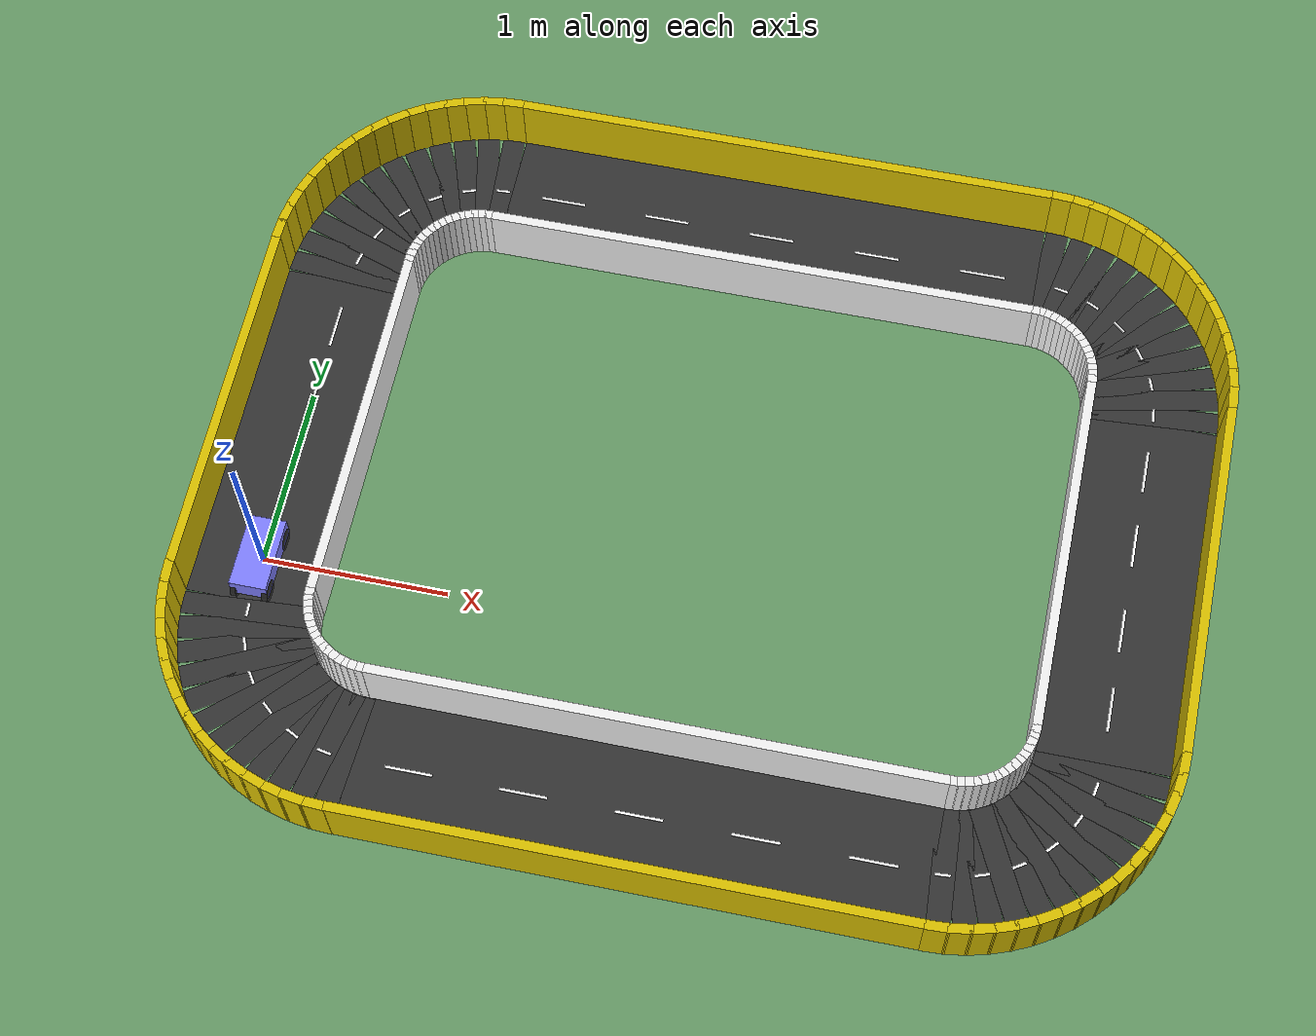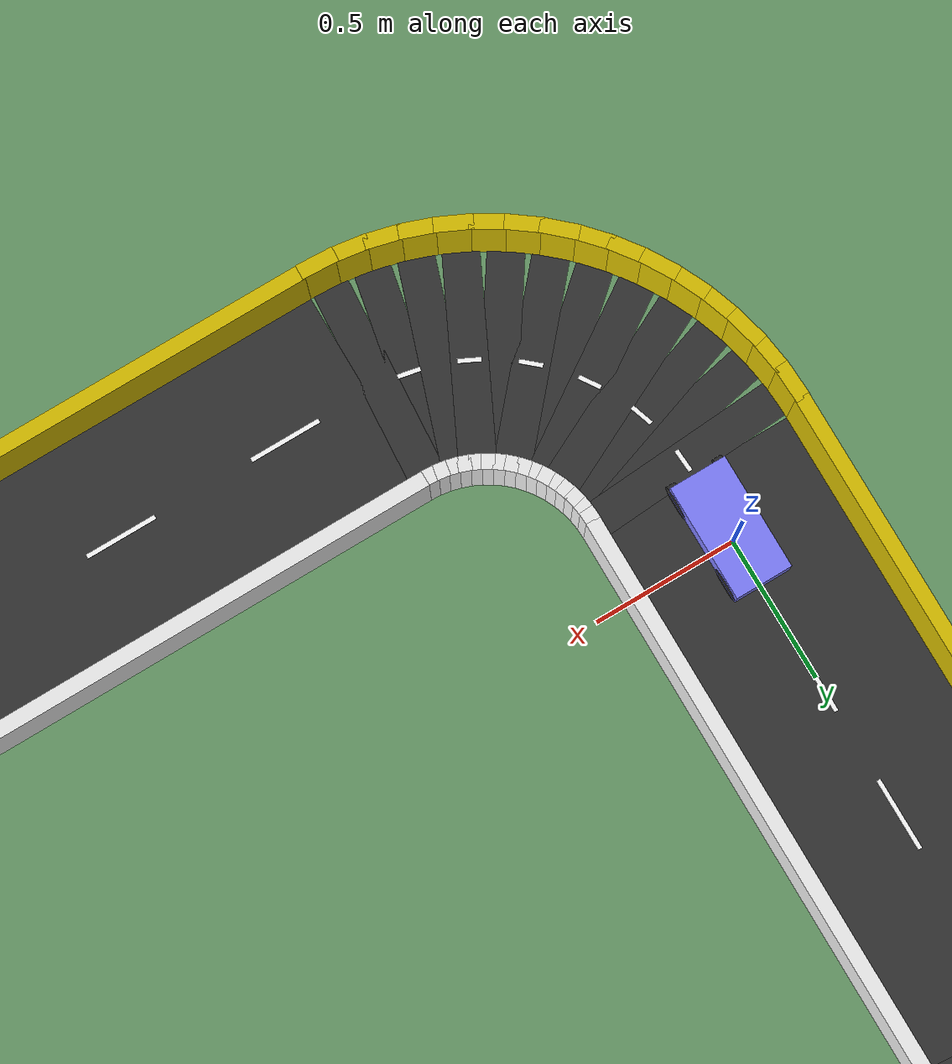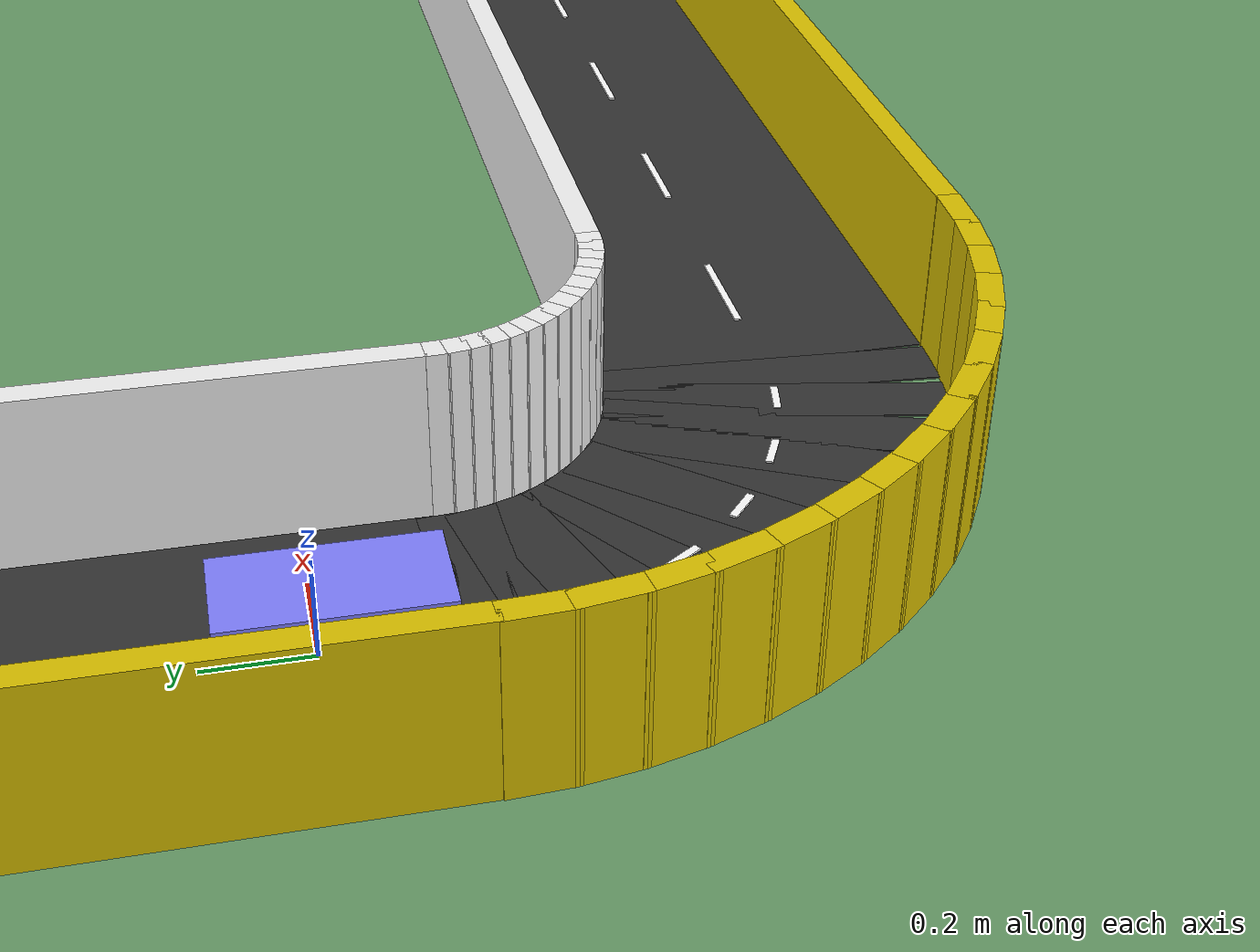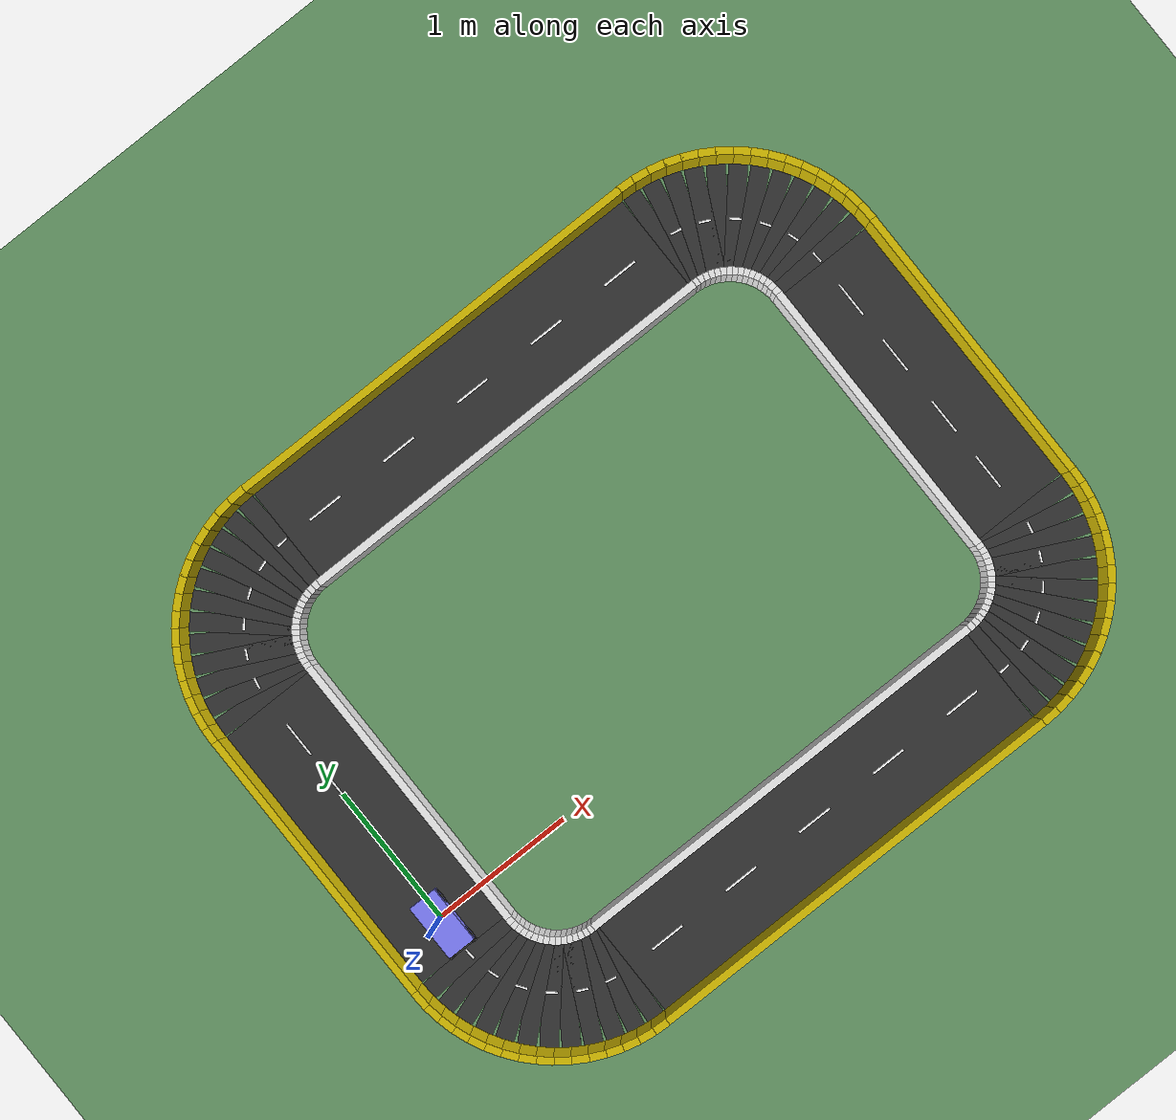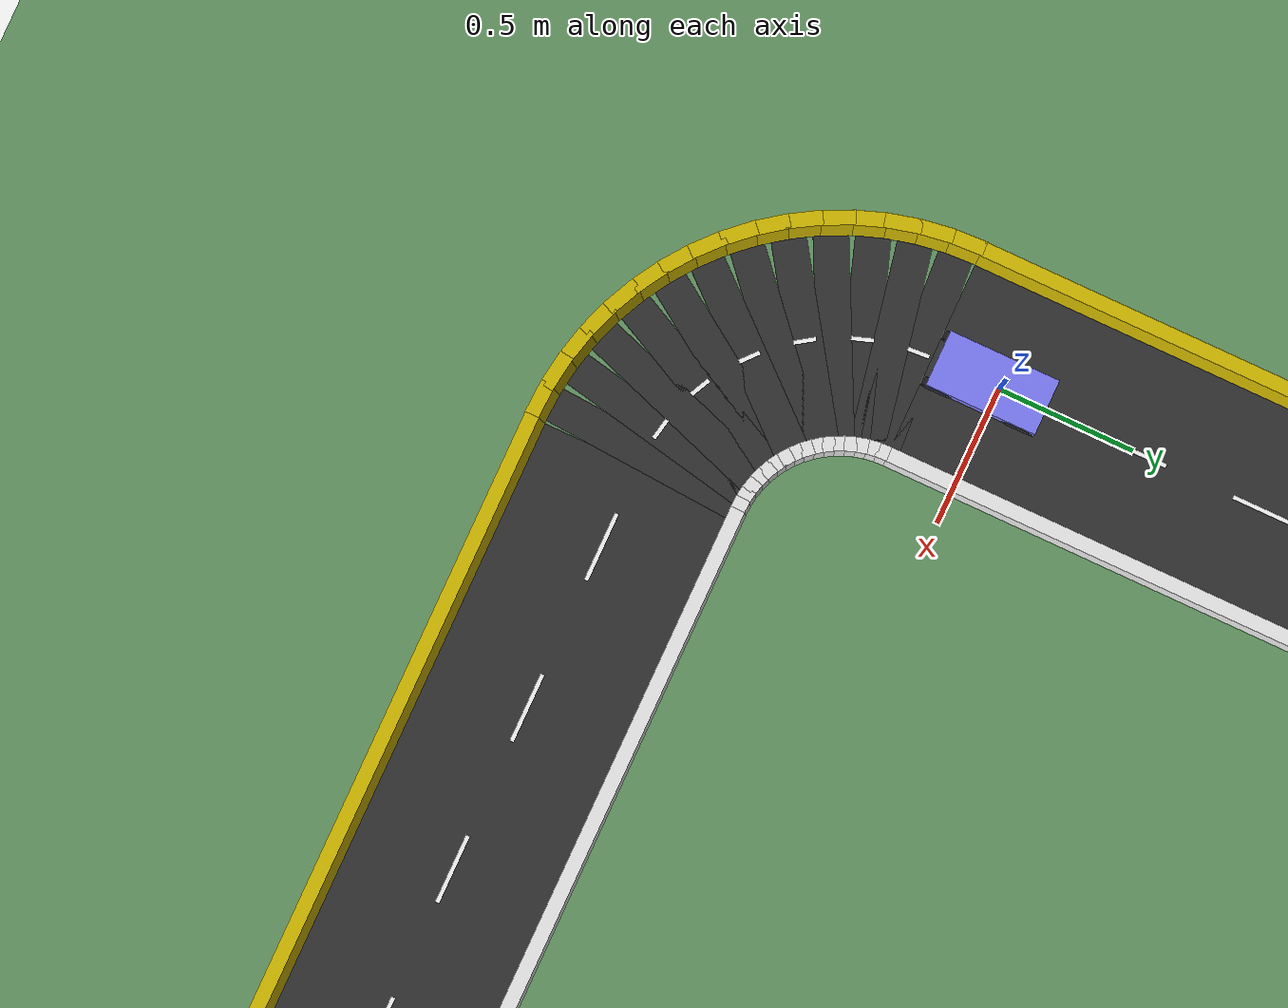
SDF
<?xml version='1.0' encoding='utf-8'?>
<sdf version="1.6">
  <world name="city_track">
    <physics name="1ms" type="ignored">
      <max_step_size>0.001</max_step_size>
      <real_time_factor>1.0</real_time_factor>
    </physics>
    <plugin filename="gz-sim-physics-system" name="gz::sim::systems::Physics" />
    <plugin filename="gz-sim-user-commands-system" name="gz::sim::systems::UserCommands" />
    <plugin filename="gz-sim-scene-broadcaster-system" name="gz::sim::systems::SceneBroadcaster" />
    <light type="directional" name="sun">
      <cast_shadows>true</cast_shadows>
      <pose>0 0 10 0 0 0</pose>
      <diffuse>1 1 1 1</diffuse>
      <specular>0.5 0.5 0.5 1</specular>
      <attenuation>
        <range>1000</range>
        <constant>0.9</constant>
        <linear>0.01</linear>
        <quadratic>0.001</quadratic>
      </attenuation>
      <direction>-0.5 0.1 -0.9</direction>
    </light>
    <model name="ground_plane">
      <static>true</static>
      <link name="link">
        <collision name="collision">
          <geometry>
            <plane>
              <normal>0 0 1</normal>
              <size>20 20</size>
            </plane>
          </geometry>
          <surface>
            <friction>
              <ode>
                <mu>50</mu>
                <mu2>50</mu2>
              </ode>
            </friction>
          </surface>
        </collision>
        <visual name="visual">
          <geometry>
            <plane>
              <normal>0 0 1</normal>
              <size>20 20</size>
            </plane>
          </geometry>
          <material>
            <ambient>0.4 0.6 0.4 1</ambient>
            <diffuse>0.4 0.6 0.4 1</diffuse>
          </material>
        </visual>
      </link>
    </model>
    <model name="road_top">
      <static>true</static>
      <pose>2.250000 2.500000 0.003000 0 0 0.000000</pose>
      <link name="link">
        <visual name="visual">
          <geometry>
            <box>
              <size>3.000000 0.700000 0.004000</size>
            </box>
          </geometry>
          <material>
            <ambient>0.2 0.2 0.2 1</ambient>
            <diffuse>0.2 0.2 0.2 1</diffuse>
          </material>
        </visual>
      </link>
    </model>
    <model name="road_bottom">
      <static>true</static>
      <pose>2.250000 -1.000000 0.003000 0 0 0.000000</pose>
      <link name="link">
        <visual name="visual">
          <geometry>
            <box>
              <size>3.000000 0.700000 0.004000</size>
            </box>
          </geometry>
          <material>
            <ambient>0.2 0.2 0.2 1</ambient>
            <diffuse>0.2 0.2 0.2 1</diffuse>
          </material>
        </visual>
      </link>
    </model>
    <model name="road_left">
      <static>true</static>
      <pose>0.000000 0.750000 0.003000 0 0 0.000000</pose>
      <link name="link">
        <visual name="visual">
          <geometry>
            <box>
              <size>0.700000 2.000000 0.004000</size>
            </box>
          </geometry>
          <material>
            <ambient>0.2 0.2 0.2 1</ambient>
            <diffuse>0.2 0.2 0.2 1</diffuse>
          </material>
        </visual>
      </link>
    </model>
    <model name="road_right">
      <static>true</static>
      <pose>4.500000 0.750000 0.003000 0 0 0.000000</pose>
      <link name="link">
        <visual name="visual">
          <geometry>
            <box>
              <size>0.700000 2.000000 0.004000</size>
            </box>
          </geometry>
          <material>
            <ambient>0.2 0.2 0.2 1</ambient>
            <diffuse>0.2 0.2 0.2 1</diffuse>
          </material>
        </visual>
      </link>
    </model>
    <model name="road_corner_tr_00">
      <static>true</static>
      <pose>4.498394 1.799052 0.003000 0 0 1.636246</pose>
      <link name="link">
        <visual name="visual">
          <geometry>
            <box>
              <size>0.122718 0.700000 0.004000</size>
            </box>
          </geometry>
          <material>
            <ambient>0.2 0.2 0.2 1</ambient>
            <diffuse>0.2 0.2 0.2 1</diffuse>
          </material>
        </visual>
      </link>
    </model>
    <model name="road_corner_tr_01">
      <static>true</static>
      <pose>4.485589 1.896318 0.003000 0 0 1.767146</pose>
      <link name="link">
        <visual name="visual">
          <geometry>
            <box>
              <size>0.122718 0.700000 0.004000</size>
            </box>
          </geometry>
          <material>
            <ambient>0.2 0.2 0.2 1</ambient>
            <diffuse>0.2 0.2 0.2 1</diffuse>
          </material>
        </visual>
      </link>
    </model>
    <model name="road_corner_tr_02">
      <static>true</static>
      <pose>4.460198 1.991080 0.003000 0 0 1.898046</pose>
      <link name="link">
        <visual name="visual">
          <geometry>
            <box>
              <size>0.122718 0.700000 0.004000</size>
            </box>
          </geometry>
          <material>
            <ambient>0.2 0.2 0.2 1</ambient>
            <diffuse>0.2 0.2 0.2 1</diffuse>
          </material>
        </visual>
      </link>
    </model>
    <model name="road_corner_tr_03">
      <static>true</static>
      <pose>4.422655 2.081717 0.003000 0 0 2.028945</pose>
      <link name="link">
        <visual name="visual">
          <geometry>
            <box>
              <size>0.122718 0.700000 0.004000</size>
            </box>
          </geometry>
          <material>
            <ambient>0.2 0.2 0.2 1</ambient>
            <diffuse>0.2 0.2 0.2 1</diffuse>
          </material>
        </visual>
      </link>
    </model>
    <model name="road_corner_tr_04">
      <static>true</static>
      <pose>4.373602 2.166678 0.003000 0 0 2.159845</pose>
      <link name="link">
        <visual name="visual">
          <geometry>
            <box>
              <size>0.122718 0.700000 0.004000</size>
            </box>
          </geometry>
          <material>
            <ambient>0.2 0.2 0.2 1</ambient>
            <diffuse>0.2 0.2 0.2 1</diffuse>
          </material>
        </visual>
      </link>
    </model>
    <model name="road_corner_tr_05">
      <static>true</static>
      <pose>4.313880 2.244509 0.003000 0 0 2.290745</pose>
      <link name="link">
        <visual name="visual">
          <geometry>
            <box>
              <size>0.122718 0.700000 0.004000</size>
            </box>
          </geometry>
          <material>
            <ambient>0.2 0.2 0.2 1</ambient>
            <diffuse>0.2 0.2 0.2 1</diffuse>
          </material>
        </visual>
      </link>
    </model>
    <model name="road_corner_tr_06">
      <static>true</static>
      <pose>4.244509 2.313880 0.003000 0 0 2.421644</pose>
      <link name="link">
        <visual name="visual">
          <geometry>
            <box>
              <size>0.122718 0.700000 0.004000</size>
            </box>
          </geometry>
          <material>
            <ambient>0.2 0.2 0.2 1</ambient>
            <diffuse>0.2 0.2 0.2 1</diffuse>
          </material>
        </visual>
      </link>
    </model>
    <model name="road_corner_tr_07">
      <static>true</static>
      <pose>4.166678 2.373602 0.003000 0 0 2.552544</pose>
      <link name="link">
        <visual name="visual">
          <geometry>
            <box>
              <size>0.122718 0.700000 0.004000</size>
            </box>
          </geometry>
          <material>
            <ambient>0.2 0.2 0.2 1</ambient>
            <diffuse>0.2 0.2 0.2 1</diffuse>
          </material>
        </visual>
      </link>
    </model>
    <model name="road_corner_tr_08">
      <static>true</static>
      <pose>4.081717 2.422655 0.003000 0 0 2.683444</pose>
      <link name="link">
        <visual name="visual">
          <geometry>
            <box>
              <size>0.122718 0.700000 0.004000</size>
            </box>
          </geometry>
          <material>
            <ambient>0.2 0.2 0.2 1</ambient>
            <diffuse>0.2 0.2 0.2 1</diffuse>
          </material>
        </visual>
      </link>
    </model>
    <model name="road_corner_tr_09">
      <static>true</static>
      <pose>3.991080 2.460198 0.003000 0 0 2.814343</pose>
      <link name="link">
        <visual name="visual">
          <geometry>
            <box>
              <size>0.122718 0.700000 0.004000</size>
            </box>
          </geometry>
          <material>
            <ambient>0.2 0.2 0.2 1</ambient>
            <diffuse>0.2 0.2 0.2 1</diffuse>
          </material>
        </visual>
      </link>
    </model>
    <model name="road_corner_tr_10">
      <static>true</static>
      <pose>3.896318 2.485589 0.003000 0 0 2.945243</pose>
      <link name="link">
        <visual name="visual">
          <geometry>
            <box>
              <size>0.122718 0.700000 0.004000</size>
            </box>
          </geometry>
          <material>
            <ambient>0.2 0.2 0.2 1</ambient>
            <diffuse>0.2 0.2 0.2 1</diffuse>
          </material>
        </visual>
      </link>
    </model>
    <model name="road_corner_tr_11">
      <static>true</static>
      <pose>3.799052 2.498394 0.003000 0 0 3.076143</pose>
      <link name="link">
        <visual name="visual">
          <geometry>
            <box>
              <size>0.122718 0.700000 0.004000</size>
            </box>
          </geometry>
          <material>
            <ambient>0.2 0.2 0.2 1</ambient>
            <diffuse>0.2 0.2 0.2 1</diffuse>
          </material>
        </visual>
      </link>
    </model>
    <model name="road_corner_tl_00">
      <static>true</static>
      <pose>0.700948 2.498394 0.003000 0 0 3.207043</pose>
      <link name="link">
        <visual name="visual">
          <geometry>
            <box>
              <size>0.122718 0.700000 0.004000</size>
            </box>
          </geometry>
          <material>
            <ambient>0.2 0.2 0.2 1</ambient>
            <diffuse>0.2 0.2 0.2 1</diffuse>
          </material>
        </visual>
      </link>
    </model>
    <model name="road_corner_tl_01">
      <static>true</static>
      <pose>0.603682 2.485589 0.003000 0 0 3.337942</pose>
      <link name="link">
        <visual name="visual">
          <geometry>
            <box>
              <size>0.122718 0.700000 0.004000</size>
            </box>
          </geometry>
          <material>
            <ambient>0.2 0.2 0.2 1</ambient>
            <diffuse>0.2 0.2 0.2 1</diffuse>
          </material>
        </visual>
      </link>
    </model>
    <model name="road_corner_tl_02">
      <static>true</static>
      <pose>0.508920 2.460198 0.003000 0 0 3.468842</pose>
      <link name="link">
        <visual name="visual">
          <geometry>
            <box>
              <size>0.122718 0.700000 0.004000</size>
            </box>
          </geometry>
          <material>
            <ambient>0.2 0.2 0.2 1</ambient>
            <diffuse>0.2 0.2 0.2 1</diffuse>
          </material>
        </visual>
      </link>
    </model>
    <model name="road_corner_tl_03">
      <static>true</static>
      <pose>0.418283 2.422655 0.003000 0 0 3.599742</pose>
      <link name="link">
        <visual name="visual">
          <geometry>
            <box>
              <size>0.122718 0.700000 0.004000</size>
            </box>
          </geometry>
          <material>
            <ambient>0.2 0.2 0.2 1</ambient>
            <diffuse>0.2 0.2 0.2 1</diffuse>
          </material>
        </visual>
      </link>
    </model>
    <model name="road_corner_tl_04">
      <static>true</static>
      <pose>0.333322 2.373602 0.003000 0 0 3.730641</pose>
      <link name="link">
        <visual name="visual">
          <geometry>
            <box>
              <size>0.122718 0.700000 0.004000</size>
            </box>
          </geometry>
          <material>
            <ambient>0.2 0.2 0.2 1</ambient>
            <diffuse>0.2 0.2 0.2 1</diffuse>
          </material>
        </visual>
      </link>
    </model>
    <model name="road_corner_tl_05">
      <static>true</static>
      <pose>0.255491 2.313880 0.003000 0 0 3.861541</pose>
      <link name="link">
        <visual name="visual">
          <geometry>
            <box>
              <size>0.122718 0.700000 0.004000</size>
            </box>
          </geometry>
          <material>
            <ambient>0.2 0.2 0.2 1</ambient>
            <diffuse>0.2 0.2 0.2 1</diffuse>
          </material>
        </visual>
      </link>
    </model>
    <model name="road_corner_tl_06">
      <static>true</static>
      <pose>0.186120 2.244509 0.003000 0 0 3.992441</pose>
      <link name="link">
        <visual name="visual">
          <geometry>
            <box>
              <size>0.122718 0.700000 0.004000</size>
            </box>
          </geometry>
          <material>
            <ambient>0.2 0.2 0.2 1</ambient>
            <diffuse>0.2 0.2 0.2 1</diffuse>
          </material>
        </visual>
      </link>
    </model>
    <model name="road_corner_tl_07">
      <static>true</static>
      <pose>0.126398 2.166678 0.003000 0 0 4.123340</pose>
      <link name="link">
        <visual name="visual">
          <geometry>
            <box>
              <size>0.122718 0.700000 0.004000</size>
            </box>
          </geometry>
          <material>
            <ambient>0.2 0.2 0.2 1</ambient>
            <diffuse>0.2 0.2 0.2 1</diffuse>
          </material>
        </visual>
      </link>
    </model>
    <model name="road_corner_tl_08">
      <static>true</static>
      <pose>0.077345 2.081717 0.003000 0 0 4.254240</pose>
      <link name="link">
        <visual name="visual">
          <geometry>
            <box>
              <size>0.122718 0.700000 0.004000</size>
            </box>
          </geometry>
          <material>
            <ambient>0.2 0.2 0.2 1</ambient>
            <diffuse>0.2 0.2 0.2 1</diffuse>
          </material>
        </visual>
      </link>
    </model>
    <model name="road_corner_tl_09">
      <static>true</static>
      <pose>0.039802 1.991080 0.003000 0 0 4.385140</pose>
      <link name="link">
        <visual name="visual">
          <geometry>
            <box>
              <size>0.122718 0.700000 0.004000</size>
            </box>
          </geometry>
          <material>
            <ambient>0.2 0.2 0.2 1</ambient>
            <diffuse>0.2 0.2 0.2 1</diffuse>
          </material>
        </visual>
      </link>
    </model>
    <model name="road_corner_tl_10">
      <static>true</static>
      <pose>0.014411 1.896318 0.003000 0 0 4.516039</pose>
      <link name="link">
        <visual name="visual">
          <geometry>
            <box>
              <size>0.122718 0.700000 0.004000</size>
            </box>
          </geometry>
          <material>
            <ambient>0.2 0.2 0.2 1</ambient>
            <diffuse>0.2 0.2 0.2 1</diffuse>
          </material>
        </visual>
      </link>
    </model>
    <model name="road_corner_tl_11">
      <static>true</static>
      <pose>0.001606 1.799052 0.003000 0 0 4.646939</pose>
      <link name="link">
        <visual name="visual">
          <geometry>
            <box>
              <size>0.122718 0.700000 0.004000</size>
            </box>
          </geometry>
          <material>
            <ambient>0.2 0.2 0.2 1</ambient>
            <diffuse>0.2 0.2 0.2 1</diffuse>
          </material>
        </visual>
      </link>
    </model>
    <model name="road_corner_bl_00">
      <static>true</static>
      <pose>0.001606 -0.299052 0.003000 0 0 4.777839</pose>
      <link name="link">
        <visual name="visual">
          <geometry>
            <box>
              <size>0.122718 0.700000 0.004000</size>
            </box>
          </geometry>
          <material>
            <ambient>0.2 0.2 0.2 1</ambient>
            <diffuse>0.2 0.2 0.2 1</diffuse>
          </material>
        </visual>
      </link>
    </model>
    <model name="road_corner_bl_01">
      <static>true</static>
      <pose>0.014411 -0.396318 0.003000 0 0 4.908739</pose>
      <link name="link">
        <visual name="visual">
          <geometry>
            <box>
              <size>0.122718 0.700000 0.004000</size>
            </box>
          </geometry>
          <material>
            <ambient>0.2 0.2 0.2 1</ambient>
            <diffuse>0.2 0.2 0.2 1</diffuse>
          </material>
        </visual>
      </link>
    </model>
    <model name="road_corner_bl_02">
      <static>true</static>
      <pose>0.039802 -0.491080 0.003000 0 0 5.039638</pose>
      <link name="link">
        <visual name="visual">
          <geometry>
            <box>
              <size>0.122718 0.700000 0.004000</size>
            </box>
          </geometry>
          <material>
            <ambient>0.2 0.2 0.2 1</ambient>
            <diffuse>0.2 0.2 0.2 1</diffuse>
          </material>
        </visual>
      </link>
    </model>
    <model name="road_corner_bl_03">
      <static>true</static>
      <pose>0.077345 -0.581717 0.003000 0 0 5.170538</pose>
      <link name="link">
        <visual name="visual">
          <geometry>
            <box>
              <size>0.122718 0.700000 0.004000</size>
            </box>
          </geometry>
          <material>
            <ambient>0.2 0.2 0.2 1</ambient>
            <diffuse>0.2 0.2 0.2 1</diffuse>
          </material>
        </visual>
      </link>
    </model>
    <model name="road_corner_bl_04">
      <static>true</static>
      <pose>0.126398 -0.666678 0.003000 0 0 5.301438</pose>
      <link name="link">
        <visual name="visual">
          <geometry>
            <box>
              <size>0.122718 0.700000 0.004000</size>
            </box>
          </geometry>
          <material>
            <ambient>0.2 0.2 0.2 1</ambient>
            <diffuse>0.2 0.2 0.2 1</diffuse>
          </material>
        </visual>
      </link>
    </model>
    <model name="road_corner_bl_05">
      <static>true</static>
      <pose>0.186120 -0.744509 0.003000 0 0 5.432337</pose>
      <link name="link">
        <visual name="visual">
          <geometry>
            <box>
              <size>0.122718 0.700000 0.004000</size>
            </box>
          </geometry>
          <material>
            <ambient>0.2 0.2 0.2 1</ambient>
            <diffuse>0.2 0.2 0.2 1</diffuse>
          </material>
        </visual>
      </link>
    </model>
    <model name="road_corner_bl_06">
      <static>true</static>
      <pose>0.255491 -0.813880 0.003000 0 0 5.563237</pose>
      <link name="link">
        <visual name="visual">
          <geometry>
            <box>
              <size>0.122718 0.700000 0.004000</size>
            </box>
          </geometry>
          <material>
            <ambient>0.2 0.2 0.2 1</ambient>
            <diffuse>0.2 0.2 0.2 1</diffuse>
          </material>
        </visual>
      </link>
    </model>
    <model name="road_corner_bl_07">
      <static>true</static>
      <pose>0.333322 -0.873602 0.003000 0 0 5.694137</pose>
      <link name="link">
        <visual name="visual">
          <geometry>
            <box>
              <size>0.122718 0.700000 0.004000</size>
            </box>
          </geometry>
          <material>
            <ambient>0.2 0.2 0.2 1</ambient>
            <diffuse>0.2 0.2 0.2 1</diffuse>
          </material>
        </visual>
      </link>
    </model>
    <model name="road_corner_bl_08">
      <static>true</static>
      <pose>0.418283 -0.922655 0.003000 0 0 5.825036</pose>
      <link name="link">
        <visual name="visual">
          <geometry>
            <box>
              <size>0.122718 0.700000 0.004000</size>
            </box>
          </geometry>
          <material>
            <ambient>0.2 0.2 0.2 1</ambient>
            <diffuse>0.2 0.2 0.2 1</diffuse>
          </material>
        </visual>
      </link>
    </model>
    <model name="road_corner_bl_09">
      <static>true</static>
      <pose>0.508920 -0.960198 0.003000 0 0 5.955936</pose>
      <link name="link">
        <visual name="visual">
          <geometry>
            <box>
              <size>0.122718 0.700000 0.004000</size>
            </box>
          </geometry>
          <material>
            <ambient>0.2 0.2 0.2 1</ambient>
            <diffuse>0.2 0.2 0.2 1</diffuse>
          </material>
        </visual>
      </link>
    </model>
    <model name="road_corner_bl_10">
      <static>true</static>
      <pose>0.603682 -0.985589 0.003000 0 0 6.086836</pose>
      <link name="link">
        <visual name="visual">
          <geometry>
            <box>
              <size>0.122718 0.700000 0.004000</size>
            </box>
          </geometry>
          <material>
            <ambient>0.2 0.2 0.2 1</ambient>
            <diffuse>0.2 0.2 0.2 1</diffuse>
          </material>
        </visual>
      </link>
    </model>
    <model name="road_corner_bl_11">
      <static>true</static>
      <pose>0.700948 -0.998394 0.003000 0 0 6.217735</pose>
      <link name="link">
        <visual name="visual">
          <geometry>
            <box>
              <size>0.122718 0.700000 0.004000</size>
            </box>
          </geometry>
          <material>
            <ambient>0.2 0.2 0.2 1</ambient>
            <diffuse>0.2 0.2 0.2 1</diffuse>
          </material>
        </visual>
      </link>
    </model>
    <model name="road_corner_br_00">
      <static>true</static>
      <pose>3.799052 -0.998394 0.003000 0 0 0.065450</pose>
      <link name="link">
        <visual name="visual">
          <geometry>
            <box>
              <size>0.122718 0.700000 0.004000</size>
            </box>
          </geometry>
          <material>
            <ambient>0.2 0.2 0.2 1</ambient>
            <diffuse>0.2 0.2 0.2 1</diffuse>
          </material>
        </visual>
      </link>
    </model>
    <model name="road_corner_br_01">
      <static>true</static>
      <pose>3.896318 -0.985589 0.003000 0 0 0.196350</pose>
      <link name="link">
        <visual name="visual">
          <geometry>
            <box>
              <size>0.122718 0.700000 0.004000</size>
            </box>
          </geometry>
          <material>
            <ambient>0.2 0.2 0.2 1</ambient>
            <diffuse>0.2 0.2 0.2 1</diffuse>
          </material>
        </visual>
      </link>
    </model>
    <model name="road_corner_br_02">
      <static>true</static>
      <pose>3.991080 -0.960198 0.003000 0 0 0.327249</pose>
      <link name="link">
        <visual name="visual">
          <geometry>
            <box>
              <size>0.122718 0.700000 0.004000</size>
            </box>
          </geometry>
          <material>
            <ambient>0.2 0.2 0.2 1</ambient>
            <diffuse>0.2 0.2 0.2 1</diffuse>
          </material>
        </visual>
      </link>
    </model>
    <model name="road_corner_br_03">
      <static>true</static>
      <pose>4.081717 -0.922655 0.003000 0 0 0.458149</pose>
      <link name="link">
        <visual name="visual">
          <geometry>
            <box>
              <size>0.122718 0.700000 0.004000</size>
            </box>
          </geometry>
          <material>
            <ambient>0.2 0.2 0.2 1</ambient>
            <diffuse>0.2 0.2 0.2 1</diffuse>
          </material>
        </visual>
      </link>
    </model>
    <model name="road_corner_br_04">
      <static>true</static>
      <pose>4.166678 -0.873602 0.003000 0 0 0.589049</pose>
      <link name="link">
        <visual name="visual">
          <geometry>
            <box>
              <size>0.122718 0.700000 0.004000</size>
            </box>
          </geometry>
          <material>
            <ambient>0.2 0.2 0.2 1</ambient>
            <diffuse>0.2 0.2 0.2 1</diffuse>
          </material>
        </visual>
      </link>
    </model>
    <model name="road_corner_br_05">
      <static>true</static>
      <pose>4.244509 -0.813880 0.003000 0 0 0.719948</pose>
      <link name="link">
        <visual name="visual">
          <geometry>
            <box>
              <size>0.122718 0.700000 0.004000</size>
            </box>
          </geometry>
          <material>
            <ambient>0.2 0.2 0.2 1</ambient>
            <diffuse>0.2 0.2 0.2 1</diffuse>
          </material>
        </visual>
      </link>
    </model>
    <model name="road_corner_br_06">
      <static>true</static>
      <pose>4.313880 -0.744509 0.003000 0 0 0.850848</pose>
      <link name="link">
        <visual name="visual">
          <geometry>
            <box>
              <size>0.122718 0.700000 0.004000</size>
            </box>
          </geometry>
          <material>
            <ambient>0.2 0.2 0.2 1</ambient>
            <diffuse>0.2 0.2 0.2 1</diffuse>
          </material>
        </visual>
      </link>
    </model>
    <model name="road_corner_br_07">
      <static>true</static>
      <pose>4.373602 -0.666678 0.003000 0 0 0.981748</pose>
      <link name="link">
        <visual name="visual">
          <geometry>
            <box>
              <size>0.122718 0.700000 0.004000</size>
            </box>
          </geometry>
          <material>
            <ambient>0.2 0.2 0.2 1</ambient>
            <diffuse>0.2 0.2 0.2 1</diffuse>
          </material>
        </visual>
      </link>
    </model>
    <model name="road_corner_br_08">
      <static>true</static>
      <pose>4.422655 -0.581717 0.003000 0 0 1.112647</pose>
      <link name="link">
        <visual name="visual">
          <geometry>
            <box>
              <size>0.122718 0.700000 0.004000</size>
            </box>
          </geometry>
          <material>
            <ambient>0.2 0.2 0.2 1</ambient>
            <diffuse>0.2 0.2 0.2 1</diffuse>
          </material>
        </visual>
      </link>
    </model>
    <model name="road_corner_br_09">
      <static>true</static>
      <pose>4.460198 -0.491080 0.003000 0 0 1.243547</pose>
      <link name="link">
        <visual name="visual">
          <geometry>
            <box>
              <size>0.122718 0.700000 0.004000</size>
            </box>
          </geometry>
          <material>
            <ambient>0.2 0.2 0.2 1</ambient>
            <diffuse>0.2 0.2 0.2 1</diffuse>
          </material>
        </visual>
      </link>
    </model>
    <model name="road_corner_br_10">
      <static>true</static>
      <pose>4.485589 -0.396318 0.003000 0 0 1.374447</pose>
      <link name="link">
        <visual name="visual">
          <geometry>
            <box>
              <size>0.122718 0.700000 0.004000</size>
            </box>
          </geometry>
          <material>
            <ambient>0.2 0.2 0.2 1</ambient>
            <diffuse>0.2 0.2 0.2 1</diffuse>
          </material>
        </visual>
      </link>
    </model>
    <model name="road_corner_br_11">
      <static>true</static>
      <pose>4.498394 -0.299052 0.003000 0 0 1.505346</pose>
      <link name="link">
        <visual name="visual">
          <geometry>
            <box>
              <size>0.122718 0.700000 0.004000</size>
            </box>
          </geometry>
          <material>
            <ambient>0.2 0.2 0.2 1</ambient>
            <diffuse>0.2 0.2 0.2 1</diffuse>
          </material>
        </visual>
      </link>
    </model>
    <model name="centerline_top_0">
      <static>true</static>
      <pose>1.050000 2.500000 0.008000 0 0 0.000000</pose>
      <link name="link">
        <visual name="visual">
          <geometry>
            <box>
              <size>0.250000 0.015000 0.004000</size>
            </box>
          </geometry>
          <material>
            <ambient>1 1 1 1</ambient>
            <diffuse>1 1 1 1</diffuse>
          </material>
        </visual>
      </link>
    </model>
    <model name="centerline_top_1">
      <static>true</static>
      <pose>1.650000 2.500000 0.008000 0 0 0.000000</pose>
      <link name="link">
        <visual name="visual">
          <geometry>
            <box>
              <size>0.250000 0.015000 0.004000</size>
            </box>
          </geometry>
          <material>
            <ambient>1 1 1 1</ambient>
            <diffuse>1 1 1 1</diffuse>
          </material>
        </visual>
      </link>
    </model>
    <model name="centerline_top_2">
      <static>true</static>
      <pose>2.250000 2.500000 0.008000 0 0 0.000000</pose>
      <link name="link">
        <visual name="visual">
          <geometry>
            <box>
              <size>0.250000 0.015000 0.004000</size>
            </box>
          </geometry>
          <material>
            <ambient>1 1 1 1</ambient>
            <diffuse>1 1 1 1</diffuse>
          </material>
        </visual>
      </link>
    </model>
    <model name="centerline_top_3">
      <static>true</static>
      <pose>2.850000 2.500000 0.008000 0 0 0.000000</pose>
      <link name="link">
        <visual name="visual">
          <geometry>
            <box>
              <size>0.250000 0.015000 0.004000</size>
            </box>
          </geometry>
          <material>
            <ambient>1 1 1 1</ambient>
            <diffuse>1 1 1 1</diffuse>
          </material>
        </visual>
      </link>
    </model>
    <model name="centerline_top_4">
      <static>true</static>
      <pose>3.450000 2.500000 0.008000 0 0 0.000000</pose>
      <link name="link">
        <visual name="visual">
          <geometry>
            <box>
              <size>0.250000 0.015000 0.004000</size>
            </box>
          </geometry>
          <material>
            <ambient>1 1 1 1</ambient>
            <diffuse>1 1 1 1</diffuse>
          </material>
        </visual>
      </link>
    </model>
    <model name="centerline_bottom_0">
      <static>true</static>
      <pose>1.050000 -1.000000 0.008000 0 0 0.000000</pose>
      <link name="link">
        <visual name="visual">
          <geometry>
            <box>
              <size>0.250000 0.015000 0.004000</size>
            </box>
          </geometry>
          <material>
            <ambient>1 1 1 1</ambient>
            <diffuse>1 1 1 1</diffuse>
          </material>
        </visual>
      </link>
    </model>
    <model name="centerline_bottom_1">
      <static>true</static>
      <pose>1.650000 -1.000000 0.008000 0 0 0.000000</pose>
      <link name="link">
        <visual name="visual">
          <geometry>
            <box>
              <size>0.250000 0.015000 0.004000</size>
            </box>
          </geometry>
          <material>
            <ambient>1 1 1 1</ambient>
            <diffuse>1 1 1 1</diffuse>
          </material>
        </visual>
      </link>
    </model>
    <model name="centerline_bottom_2">
      <static>true</static>
      <pose>2.250000 -1.000000 0.008000 0 0 0.000000</pose>
      <link name="link">
        <visual name="visual">
          <geometry>
            <box>
              <size>0.250000 0.015000 0.004000</size>
            </box>
          </geometry>
          <material>
            <ambient>1 1 1 1</ambient>
            <diffuse>1 1 1 1</diffuse>
          </material>
        </visual>
      </link>
    </model>
    <model name="centerline_bottom_3">
      <static>true</static>
      <pose>2.850000 -1.000000 0.008000 0 0 0.000000</pose>
      <link name="link">
        <visual name="visual">
          <geometry>
            <box>
              <size>0.250000 0.015000 0.004000</size>
            </box>
          </geometry>
          <material>
            <ambient>1 1 1 1</ambient>
            <diffuse>1 1 1 1</diffuse>
          </material>
        </visual>
      </link>
    </model>
    <model name="centerline_bottom_4">
      <static>true</static>
      <pose>3.450000 -1.000000 0.008000 0 0 0.000000</pose>
      <link name="link">
        <visual name="visual">
          <geometry>
            <box>
              <size>0.250000 0.015000 0.004000</size>
            </box>
          </geometry>
          <material>
            <ambient>1 1 1 1</ambient>
            <diffuse>1 1 1 1</diffuse>
          </material>
        </visual>
      </link>
    </model>
    <model name="centerline_left_0">
      <static>true</static>
      <pose>0.000000 0.050000 0.008000 0 0 0.000000</pose>
      <link name="link">
        <visual name="visual">
          <geometry>
            <box>
              <size>0.015000 0.250000 0.004000</size>
            </box>
          </geometry>
          <material>
            <ambient>1 1 1 1</ambient>
            <diffuse>1 1 1 1</diffuse>
          </material>
        </visual>
      </link>
    </model>
    <model name="centerline_left_1">
      <static>true</static>
      <pose>0.000000 0.500000 0.008000 0 0 0.000000</pose>
      <link name="link">
        <visual name="visual">
          <geometry>
            <box>
              <size>0.015000 0.250000 0.004000</size>
            </box>
          </geometry>
          <material>
            <ambient>1 1 1 1</ambient>
            <diffuse>1 1 1 1</diffuse>
          </material>
        </visual>
      </link>
    </model>
    <model name="centerline_left_2">
      <static>true</static>
      <pose>0.000000 1.000000 0.008000 0 0 0.000000</pose>
      <link name="link">
        <visual name="visual">
          <geometry>
            <box>
              <size>0.015000 0.250000 0.004000</size>
            </box>
          </geometry>
          <material>
            <ambient>1 1 1 1</ambient>
            <diffuse>1 1 1 1</diffuse>
          </material>
        </visual>
      </link>
    </model>
    <model name="centerline_left_3">
      <static>true</static>
      <pose>0.000000 1.450000 0.008000 0 0 0.000000</pose>
      <link name="link">
        <visual name="visual">
          <geometry>
            <box>
              <size>0.015000 0.250000 0.004000</size>
            </box>
          </geometry>
          <material>
            <ambient>1 1 1 1</ambient>
            <diffuse>1 1 1 1</diffuse>
          </material>
        </visual>
      </link>
    </model>
    <model name="centerline_right_0">
      <static>true</static>
      <pose>4.500000 0.050000 0.008000 0 0 0.000000</pose>
      <link name="link">
        <visual name="visual">
          <geometry>
            <box>
              <size>0.015000 0.250000 0.004000</size>
            </box>
          </geometry>
          <material>
            <ambient>1 1 1 1</ambient>
            <diffuse>1 1 1 1</diffuse>
          </material>
        </visual>
      </link>
    </model>
    <model name="centerline_right_1">
      <static>true</static>
      <pose>4.500000 0.500000 0.008000 0 0 0.000000</pose>
      <link name="link">
        <visual name="visual">
          <geometry>
            <box>
              <size>0.015000 0.250000 0.004000</size>
            </box>
          </geometry>
          <material>
            <ambient>1 1 1 1</ambient>
            <diffuse>1 1 1 1</diffuse>
          </material>
        </visual>
      </link>
    </model>
    <model name="centerline_right_2">
      <static>true</static>
      <pose>4.500000 1.000000 0.008000 0 0 0.000000</pose>
      <link name="link">
        <visual name="visual">
          <geometry>
            <box>
              <size>0.015000 0.250000 0.004000</size>
            </box>
          </geometry>
          <material>
            <ambient>1 1 1 1</ambient>
            <diffuse>1 1 1 1</diffuse>
          </material>
        </visual>
      </link>
    </model>
    <model name="centerline_right_3">
      <static>true</static>
      <pose>4.500000 1.450000 0.008000 0 0 0.000000</pose>
      <link name="link">
        <visual name="visual">
          <geometry>
            <box>
              <size>0.015000 0.250000 0.004000</size>
            </box>
          </geometry>
          <material>
            <ambient>1 1 1 1</ambient>
            <diffuse>1 1 1 1</diffuse>
          </material>
        </visual>
      </link>
    </model>
    <model name="centerline_road_corner_tr_00">
      <static>true</static>
      <pose>4.498394 1.799052 0.010000 0 0 1.636246</pose>
      <link name="link">
        <visual name="visual">
          <geometry>
            <box>
              <size>0.078540 0.015000 0.004000</size>
            </box>
          </geometry>
          <material>
            <ambient>1 1 1 1</ambient>
            <diffuse>1 1 1 1</diffuse>
          </material>
        </visual>
      </link>
    </model>
    <model name="centerline_road_corner_tr_02">
      <static>true</static>
      <pose>4.460198 1.991080 0.010000 0 0 1.898046</pose>
      <link name="link">
        <visual name="visual">
          <geometry>
            <box>
              <size>0.078540 0.015000 0.004000</size>
            </box>
          </geometry>
          <material>
            <ambient>1 1 1 1</ambient>
            <diffuse>1 1 1 1</diffuse>
          </material>
        </visual>
      </link>
    </model>
    <model name="centerline_road_corner_tr_04">
      <static>true</static>
      <pose>4.373602 2.166678 0.010000 0 0 2.159845</pose>
      <link name="link">
        <visual name="visual">
          <geometry>
            <box>
              <size>0.078540 0.015000 0.004000</size>
            </box>
          </geometry>
          <material>
            <ambient>1 1 1 1</ambient>
            <diffuse>1 1 1 1</diffuse>
          </material>
        </visual>
      </link>
    </model>
    <model name="centerline_road_corner_tr_06">
      <static>true</static>
      <pose>4.244509 2.313880 0.010000 0 0 2.421644</pose>
      <link name="link">
        <visual name="visual">
          <geometry>
            <box>
              <size>0.078540 0.015000 0.004000</size>
            </box>
          </geometry>
          <material>
            <ambient>1 1 1 1</ambient>
            <diffuse>1 1 1 1</diffuse>
          </material>
        </visual>
      </link>
    </model>
    <model name="centerline_road_corner_tr_08">
      <static>true</static>
      <pose>4.081717 2.422655 0.010000 0 0 2.683444</pose>
      <link name="link">
        <visual name="visual">
          <geometry>
            <box>
              <size>0.078540 0.015000 0.004000</size>
            </box>
          </geometry>
          <material>
            <ambient>1 1 1 1</ambient>
            <diffuse>1 1 1 1</diffuse>
          </material>
        </visual>
      </link>
    </model>
    <model name="centerline_road_corner_tr_10">
      <static>true</static>
      <pose>3.896318 2.485589 0.010000 0 0 2.945243</pose>
      <link name="link">
        <visual name="visual">
          <geometry>
            <box>
              <size>0.078540 0.015000 0.004000</size>
            </box>
          </geometry>
          <material>
            <ambient>1 1 1 1</ambient>
            <diffuse>1 1 1 1</diffuse>
          </material>
        </visual>
      </link>
    </model>
    <model name="centerline_road_corner_tl_00">
      <static>true</static>
      <pose>0.700948 2.498394 0.010000 0 0 3.207043</pose>
      <link name="link">
        <visual name="visual">
          <geometry>
            <box>
              <size>0.078540 0.015000 0.004000</size>
            </box>
          </geometry>
          <material>
            <ambient>1 1 1 1</ambient>
            <diffuse>1 1 1 1</diffuse>
          </material>
        </visual>
      </link>
    </model>
    <model name="centerline_road_corner_tl_02">
      <static>true</static>
      <pose>0.508920 2.460198 0.010000 0 0 3.468842</pose>
      <link name="link">
        <visual name="visual">
          <geometry>
            <box>
              <size>0.078540 0.015000 0.004000</size>
            </box>
          </geometry>
          <material>
            <ambient>1 1 1 1</ambient>
            <diffuse>1 1 1 1</diffuse>
          </material>
        </visual>
      </link>
    </model>
    <model name="centerline_road_corner_tl_04">
      <static>true</static>
      <pose>0.333322 2.373602 0.010000 0 0 3.730641</pose>
      <link name="link">
        <visual name="visual">
          <geometry>
            <box>
              <size>0.078540 0.015000 0.004000</size>
            </box>
          </geometry>
          <material>
            <ambient>1 1 1 1</ambient>
            <diffuse>1 1 1 1</diffuse>
          </material>
        </visual>
      </link>
    </model>
    <model name="centerline_road_corner_tl_06">
      <static>true</static>
      <pose>0.186120 2.244509 0.010000 0 0 3.992441</pose>
      <link name="link">
        <visual name="visual">
          <geometry>
            <box>
              <size>0.078540 0.015000 0.004000</size>
            </box>
          </geometry>
          <material>
            <ambient>1 1 1 1</ambient>
            <diffuse>1 1 1 1</diffuse>
          </material>
        </visual>
      </link>
    </model>
    <model name="centerline_road_corner_tl_08">
      <static>true</static>
      <pose>0.077345 2.081717 0.010000 0 0 4.254240</pose>
      <link name="link">
        <visual name="visual">
          <geometry>
            <box>
              <size>0.078540 0.015000 0.004000</size>
            </box>
          </geometry>
          <material>
            <ambient>1 1 1 1</ambient>
            <diffuse>1 1 1 1</diffuse>
          </material>
        </visual>
      </link>
    </model>
    <model name="centerline_road_corner_tl_10">
      <static>true</static>
      <pose>0.014411 1.896318 0.010000 0 0 4.516039</pose>
      <link name="link">
        <visual name="visual">
          <geometry>
            <box>
              <size>0.078540 0.015000 0.004000</size>
            </box>
          </geometry>
          <material>
            <ambient>1 1 1 1</ambient>
            <diffuse>1 1 1 1</diffuse>
          </material>
        </visual>
      </link>
    </model>
    <model name="centerline_road_corner_bl_00">
      <static>true</static>
      <pose>0.001606 -0.299052 0.010000 0 0 4.777839</pose>
      <link name="link">
        <visual name="visual">
          <geometry>
            <box>
              <size>0.078540 0.015000 0.004000</size>
            </box>
          </geometry>
          <material>
            <ambient>1 1 1 1</ambient>
            <diffuse>1 1 1 1</diffuse>
          </material>
        </visual>
      </link>
    </model>
    <model name="centerline_road_corner_bl_02">
      <static>true</static>
      <pose>0.039802 -0.491080 0.010000 0 0 5.039638</pose>
      <link name="link">
        <visual name="visual">
          <geometry>
            <box>
              <size>0.078540 0.015000 0.004000</size>
            </box>
          </geometry>
          <material>
            <ambient>1 1 1 1</ambient>
            <diffuse>1 1 1 1</diffuse>
          </material>
        </visual>
      </link>
    </model>
    <model name="centerline_road_corner_bl_04">
      <static>true</static>
      <pose>0.126398 -0.666678 0.010000 0 0 5.301438</pose>
      <link name="link">
        <visual name="visual">
          <geometry>
            <box>
              <size>0.078540 0.015000 0.004000</size>
            </box>
          </geometry>
          <material>
            <ambient>1 1 1 1</ambient>
            <diffuse>1 1 1 1</diffuse>
          </material>
        </visual>
      </link>
    </model>
    <model name="centerline_road_corner_bl_06">
      <static>true</static>
      <pose>0.255491 -0.813880 0.010000 0 0 5.563237</pose>
      <link name="link">
        <visual name="visual">
          <geometry>
            <box>
              <size>0.078540 0.015000 0.004000</size>
            </box>
          </geometry>
          <material>
            <ambient>1 1 1 1</ambient>
            <diffuse>1 1 1 1</diffuse>
          </material>
        </visual>
      </link>
    </model>
    <model name="centerline_road_corner_bl_08">
      <static>true</static>
      <pose>0.418283 -0.922655 0.010000 0 0 5.825036</pose>
      <link name="link">
        <visual name="visual">
          <geometry>
            <box>
              <size>0.078540 0.015000 0.004000</size>
            </box>
          </geometry>
          <material>
            <ambient>1 1 1 1</ambient>
            <diffuse>1 1 1 1</diffuse>
          </material>
        </visual>
      </link>
    </model>
    <model name="centerline_road_corner_bl_10">
      <static>true</static>
      <pose>0.603682 -0.985589 0.010000 0 0 6.086836</pose>
      <link name="link">
        <visual name="visual">
          <geometry>
            <box>
              <size>0.078540 0.015000 0.004000</size>
            </box>
          </geometry>
          <material>
            <ambient>1 1 1 1</ambient>
            <diffuse>1 1 1 1</diffuse>
          </material>
        </visual>
      </link>
    </model>
    <model name="centerline_road_corner_br_00">
      <static>true</static>
      <pose>3.799052 -0.998394 0.010000 0 0 0.065450</pose>
      <link name="link">
        <visual name="visual">
          <geometry>
            <box>
              <size>0.078540 0.015000 0.004000</size>
            </box>
          </geometry>
          <material>
            <ambient>1 1 1 1</ambient>
            <diffuse>1 1 1 1</diffuse>
          </material>
        </visual>
      </link>
    </model>
    <model name="centerline_road_corner_br_02">
      <static>true</static>
      <pose>3.991080 -0.960198 0.010000 0 0 0.327249</pose>
      <link name="link">
        <visual name="visual">
          <geometry>
            <box>
              <size>0.078540 0.015000 0.004000</size>
            </box>
          </geometry>
          <material>
            <ambient>1 1 1 1</ambient>
            <diffuse>1 1 1 1</diffuse>
          </material>
        </visual>
      </link>
    </model>
    <model name="centerline_road_corner_br_04">
      <static>true</static>
      <pose>4.166678 -0.873602 0.010000 0 0 0.589049</pose>
      <link name="link">
        <visual name="visual">
          <geometry>
            <box>
              <size>0.078540 0.015000 0.004000</size>
            </box>
          </geometry>
          <material>
            <ambient>1 1 1 1</ambient>
            <diffuse>1 1 1 1</diffuse>
          </material>
        </visual>
      </link>
    </model>
    <model name="centerline_road_corner_br_06">
      <static>true</static>
      <pose>4.313880 -0.744509 0.010000 0 0 0.850848</pose>
      <link name="link">
        <visual name="visual">
          <geometry>
            <box>
              <size>0.078540 0.015000 0.004000</size>
            </box>
          </geometry>
          <material>
            <ambient>1 1 1 1</ambient>
            <diffuse>1 1 1 1</diffuse>
          </material>
        </visual>
      </link>
    </model>
    <model name="centerline_road_corner_br_08">
      <static>true</static>
      <pose>4.422655 -0.581717 0.010000 0 0 1.112647</pose>
      <link name="link">
        <visual name="visual">
          <geometry>
            <box>
              <size>0.078540 0.015000 0.004000</size>
            </box>
          </geometry>
          <material>
            <ambient>1 1 1 1</ambient>
            <diffuse>1 1 1 1</diffuse>
          </material>
        </visual>
      </link>
    </model>
    <model name="centerline_road_corner_br_10">
      <static>true</static>
      <pose>4.485589 -0.396318 0.010000 0 0 1.374447</pose>
      <link name="link">
        <visual name="visual">
          <geometry>
            <box>
              <size>0.078540 0.015000 0.004000</size>
            </box>
          </geometry>
          <material>
            <ambient>1 1 1 1</ambient>
            <diffuse>1 1 1 1</diffuse>
          </material>
        </visual>
      </link>
    </model>
    <model name="outer_wall_top">
      <static>true</static>
      <pose>2.250000 2.875000 0.175000 0 0 0.000000</pose>
      <link name="link">
        <collision name="collision">
          <geometry>
            <box>
              <size>3.000000 0.050000 0.350000</size>
            </box>
          </geometry>
        </collision>
        <visual name="visual">
          <geometry>
            <box>
              <size>3.000000 0.050000 0.350000</size>
            </box>
          </geometry>
          <material>
            <ambient>0.85 0.75 0.0 1</ambient>
            <diffuse>0.85 0.75 0.0 1</diffuse>
          </material>
        </visual>
      </link>
    </model>
    <model name="outer_wall_bottom">
      <static>true</static>
      <pose>2.250000 -1.375000 0.175000 0 0 0.000000</pose>
      <link name="link">
        <collision name="collision">
          <geometry>
            <box>
              <size>3.000000 0.050000 0.350000</size>
            </box>
          </geometry>
        </collision>
        <visual name="visual">
          <geometry>
            <box>
              <size>3.000000 0.050000 0.350000</size>
            </box>
          </geometry>
          <material>
            <ambient>0.85 0.75 0.0 1</ambient>
            <diffuse>0.85 0.75 0.0 1</diffuse>
          </material>
        </visual>
      </link>
    </model>
    <model name="outer_wall_left">
      <static>true</static>
      <pose>-0.375000 0.750000 0.175000 0 0 0.000000</pose>
      <link name="link">
        <collision name="collision">
          <geometry>
            <box>
              <size>0.050000 2.000000 0.350000</size>
            </box>
          </geometry>
        </collision>
        <visual name="visual">
          <geometry>
            <box>
              <size>0.050000 2.000000 0.350000</size>
            </box>
          </geometry>
          <material>
            <ambient>0.85 0.75 0.0 1</ambient>
            <diffuse>0.85 0.75 0.0 1</diffuse>
          </material>
        </visual>
      </link>
    </model>
    <model name="outer_wall_right">
      <static>true</static>
      <pose>4.875000 0.750000 0.175000 0 0 0.000000</pose>
      <link name="link">
        <collision name="collision">
          <geometry>
            <box>
              <size>0.050000 2.000000 0.350000</size>
            </box>
          </geometry>
        </collision>
        <visual name="visual">
          <geometry>
            <box>
              <size>0.050000 2.000000 0.350000</size>
            </box>
          </geometry>
          <material>
            <ambient>0.85 0.75 0.0 1</ambient>
            <diffuse>0.85 0.75 0.0 1</diffuse>
          </material>
        </visual>
      </link>
    </model>
    <model name="inner_wall_top">
      <static>true</static>
      <pose>2.250000 2.125000 0.175000 0 0 0.000000</pose>
      <link name="link">
        <collision name="collision">
          <geometry>
            <box>
              <size>3.000000 0.050000 0.350000</size>
            </box>
          </geometry>
        </collision>
        <visual name="visual">
          <geometry>
            <box>
              <size>3.000000 0.050000 0.350000</size>
            </box>
          </geometry>
          <material>
            <ambient>0.95 0.95 0.95 1</ambient>
            <diffuse>0.95 0.95 0.95 1</diffuse>
          </material>
        </visual>
      </link>
    </model>
    <model name="inner_wall_bottom">
      <static>true</static>
      <pose>2.250000 -0.625000 0.175000 0 0 0.000000</pose>
      <link name="link">
        <collision name="collision">
          <geometry>
            <box>
              <size>3.000000 0.050000 0.350000</size>
            </box>
          </geometry>
        </collision>
        <visual name="visual">
          <geometry>
            <box>
              <size>3.000000 0.050000 0.350000</size>
            </box>
          </geometry>
          <material>
            <ambient>0.95 0.95 0.95 1</ambient>
            <diffuse>0.95 0.95 0.95 1</diffuse>
          </material>
        </visual>
      </link>
    </model>
    <model name="inner_wall_left">
      <static>true</static>
      <pose>0.375000 0.750000 0.175000 0 0 0.000000</pose>
      <link name="link">
        <collision name="collision">
          <geometry>
            <box>
              <size>0.050000 2.000000 0.350000</size>
            </box>
          </geometry>
        </collision>
        <visual name="visual">
          <geometry>
            <box>
              <size>0.050000 2.000000 0.350000</size>
            </box>
          </geometry>
          <material>
            <ambient>0.95 0.95 0.95 1</ambient>
            <diffuse>0.95 0.95 0.95 1</diffuse>
          </material>
        </visual>
      </link>
    </model>
    <model name="inner_wall_right">
      <static>true</static>
      <pose>4.125000 0.750000 0.175000 0 0 0.000000</pose>
      <link name="link">
        <collision name="collision">
          <geometry>
            <box>
              <size>0.050000 2.000000 0.350000</size>
            </box>
          </geometry>
        </collision>
        <visual name="visual">
          <geometry>
            <box>
              <size>0.050000 2.000000 0.350000</size>
            </box>
          </geometry>
          <material>
            <ambient>0.95 0.95 0.95 1</ambient>
            <diffuse>0.95 0.95 0.95 1</diffuse>
          </material>
        </visual>
      </link>
    </model>
    <model name="outer_wall_corner_tr_00">
      <static>true</static>
      <pose>4.873645 1.805201 0.175000 0 0 1.619884</pose>
      <link name="link">
        <collision name="collision">
          <geometry>
            <box>
              <size>0.127014 0.050000 0.350000</size>
            </box>
          </geometry>
        </collision>
        <visual name="visual">
          <geometry>
            <box>
              <size>0.127014 0.050000 0.350000</size>
            </box>
          </geometry>
          <material>
            <ambient>0.85 0.75 0.0 1</ambient>
            <diffuse>0.85 0.75 0.0 1</diffuse>
          </material>
        </visual>
      </link>
    </model>
    <model name="inner_wall_corner_tr_00">
      <static>true</static>
      <pose>4.124548 1.768400 0.175000 0 0 1.619884</pose>
      <link name="link">
        <collision name="collision">
          <geometry>
            <box>
              <size>0.044179 0.050000 0.350000</size>
            </box>
          </geometry>
        </collision>
        <visual name="visual">
          <geometry>
            <box>
              <size>0.044179 0.050000 0.350000</size>
            </box>
          </geometry>
          <material>
            <ambient>0.95 0.95 0.95 1</ambient>
            <diffuse>0.95 0.95 0.95 1</diffuse>
          </material>
        </visual>
      </link>
    </model>
    <model name="outer_wall_corner_tr_01">
      <static>true</static>
      <pose>4.862824 1.915072 0.175000 0 0 1.718058</pose>
      <link name="link">
        <collision name="collision">
          <geometry>
            <box>
              <size>0.127014 0.050000 0.350000</size>
            </box>
          </geometry>
        </collision>
        <visual name="visual">
          <geometry>
            <box>
              <size>0.127014 0.050000 0.350000</size>
            </box>
          </geometry>
          <material>
            <ambient>0.85 0.75 0.0 1</ambient>
            <diffuse>0.85 0.75 0.0 1</diffuse>
          </material>
        </visual>
      </link>
    </model>
    <model name="inner_wall_corner_tr_01">
      <static>true</static>
      <pose>4.120941 1.805024 0.175000 0 0 1.718058</pose>
      <link name="link">
        <collision name="collision">
          <geometry>
            <box>
              <size>0.044179 0.050000 0.350000</size>
            </box>
          </geometry>
        </collision>
        <visual name="visual">
          <geometry>
            <box>
              <size>0.044179 0.050000 0.350000</size>
            </box>
          </geometry>
          <material>
            <ambient>0.95 0.95 0.95 1</ambient>
            <diffuse>0.95 0.95 0.95 1</diffuse>
          </material>
        </visual>
      </link>
    </model>
    <model name="outer_wall_corner_tr_02">
      <static>true</static>
      <pose>4.841285 2.023353 0.175000 0 0 1.816233</pose>
      <link name="link">
        <collision name="collision">
          <geometry>
            <box>
              <size>0.127014 0.050000 0.350000</size>
            </box>
          </geometry>
        </collision>
        <visual name="visual">
          <geometry>
            <box>
              <size>0.127014 0.050000 0.350000</size>
            </box>
          </geometry>
          <material>
            <ambient>0.85 0.75 0.0 1</ambient>
            <diffuse>0.85 0.75 0.0 1</diffuse>
          </material>
        </visual>
      </link>
    </model>
    <model name="inner_wall_corner_tr_02">
      <static>true</static>
      <pose>4.113762 1.841118 0.175000 0 0 1.816233</pose>
      <link name="link">
        <collision name="collision">
          <geometry>
            <box>
              <size>0.044179 0.050000 0.350000</size>
            </box>
          </geometry>
        </collision>
        <visual name="visual">
          <geometry>
            <box>
              <size>0.044179 0.050000 0.350000</size>
            </box>
          </geometry>
          <material>
            <ambient>0.95 0.95 0.95 1</ambient>
            <diffuse>0.95 0.95 0.95 1</diffuse>
          </material>
        </visual>
      </link>
    </model>
    <model name="outer_wall_corner_tr_03">
      <static>true</static>
      <pose>4.809237 2.129001 0.175000 0 0 1.914408</pose>
      <link name="link">
        <collision name="collision">
          <geometry>
            <box>
              <size>0.127014 0.050000 0.350000</size>
            </box>
          </geometry>
        </collision>
        <visual name="visual">
          <geometry>
            <box>
              <size>0.127014 0.050000 0.350000</size>
            </box>
          </geometry>
          <material>
            <ambient>0.85 0.75 0.0 1</ambient>
            <diffuse>0.85 0.75 0.0 1</diffuse>
          </material>
        </visual>
      </link>
    </model>
    <model name="inner_wall_corner_tr_03">
      <static>true</static>
      <pose>4.103079 1.876334 0.175000 0 0 1.914408</pose>
      <link name="link">
        <collision name="collision">
          <geometry>
            <box>
              <size>0.044179 0.050000 0.350000</size>
            </box>
          </geometry>
        </collision>
        <visual name="visual">
          <geometry>
            <box>
              <size>0.044179 0.050000 0.350000</size>
            </box>
          </geometry>
          <material>
            <ambient>0.95 0.95 0.95 1</ambient>
            <diffuse>0.95 0.95 0.95 1</diffuse>
          </material>
        </visual>
      </link>
    </model>
    <model name="outer_wall_corner_tr_04">
      <static>true</static>
      <pose>4.766988 2.231000 0.175000 0 0 2.012583</pose>
      <link name="link">
        <collision name="collision">
          <geometry>
            <box>
              <size>0.127014 0.050000 0.350000</size>
            </box>
          </geometry>
        </collision>
        <visual name="visual">
          <geometry>
            <box>
              <size>0.127014 0.050000 0.350000</size>
            </box>
          </geometry>
          <material>
            <ambient>0.85 0.75 0.0 1</ambient>
            <diffuse>0.85 0.75 0.0 1</diffuse>
          </material>
        </visual>
      </link>
    </model>
    <model name="inner_wall_corner_tr_04">
      <static>true</static>
      <pose>4.088996 1.910333 0.175000 0 0 2.012583</pose>
      <link name="link">
        <collision name="collision">
          <geometry>
            <box>
              <size>0.044179 0.050000 0.350000</size>
            </box>
          </geometry>
        </collision>
        <visual name="visual">
          <geometry>
            <box>
              <size>0.044179 0.050000 0.350000</size>
            </box>
          </geometry>
          <material>
            <ambient>0.95 0.95 0.95 1</ambient>
            <diffuse>0.95 0.95 0.95 1</diffuse>
          </material>
        </visual>
      </link>
    </model>
    <model name="outer_wall_corner_tr_05">
      <static>true</static>
      <pose>4.714945 2.328365 0.175000 0 0 2.110758</pose>
      <link name="link">
        <collision name="collision">
          <geometry>
            <box>
              <size>0.127014 0.050000 0.350000</size>
            </box>
          </geometry>
        </collision>
        <visual name="visual">
          <geometry>
            <box>
              <size>0.127014 0.050000 0.350000</size>
            </box>
          </geometry>
          <material>
            <ambient>0.85 0.75 0.0 1</ambient>
            <diffuse>0.85 0.75 0.0 1</diffuse>
          </material>
        </visual>
      </link>
    </model>
    <model name="inner_wall_corner_tr_05">
      <static>true</static>
      <pose>4.071648 1.942789 0.175000 0 0 2.110758</pose>
      <link name="link">
        <collision name="collision">
          <geometry>
            <box>
              <size>0.044179 0.050000 0.350000</size>
            </box>
          </geometry>
        </collision>
        <visual name="visual">
          <geometry>
            <box>
              <size>0.044179 0.050000 0.350000</size>
            </box>
          </geometry>
          <material>
            <ambient>0.95 0.95 0.95 1</ambient>
            <diffuse>0.95 0.95 0.95 1</diffuse>
          </material>
        </visual>
      </link>
    </model>
    <model name="outer_wall_corner_tr_06">
      <static>true</static>
      <pose>4.653608 2.420162 0.175000 0 0 2.208932</pose>
      <link name="link">
        <collision name="collision">
          <geometry>
            <box>
              <size>0.127014 0.050000 0.350000</size>
            </box>
          </geometry>
        </collision>
        <visual name="visual">
          <geometry>
            <box>
              <size>0.127014 0.050000 0.350000</size>
            </box>
          </geometry>
          <material>
            <ambient>0.85 0.75 0.0 1</ambient>
            <diffuse>0.85 0.75 0.0 1</diffuse>
          </material>
        </visual>
      </link>
    </model>
    <model name="inner_wall_corner_tr_06">
      <static>true</static>
      <pose>4.051203 1.973387 0.175000 0 0 2.208932</pose>
      <link name="link">
        <collision name="collision">
          <geometry>
            <box>
              <size>0.044179 0.050000 0.350000</size>
            </box>
          </geometry>
        </collision>
        <visual name="visual">
          <geometry>
            <box>
              <size>0.044179 0.050000 0.350000</size>
            </box>
          </geometry>
          <material>
            <ambient>0.95 0.95 0.95 1</ambient>
            <diffuse>0.95 0.95 0.95 1</diffuse>
          </material>
        </visual>
      </link>
    </model>
    <model name="outer_wall_corner_tr_07">
      <static>true</static>
      <pose>4.583570 2.505504 0.175000 0 0 2.307107</pose>
      <link name="link">
        <collision name="collision">
          <geometry>
            <box>
              <size>0.127014 0.050000 0.350000</size>
            </box>
          </geometry>
        </collision>
        <visual name="visual">
          <geometry>
            <box>
              <size>0.127014 0.050000 0.350000</size>
            </box>
          </geometry>
          <material>
            <ambient>0.85 0.75 0.0 1</ambient>
            <diffuse>0.85 0.75 0.0 1</diffuse>
          </material>
        </visual>
      </link>
    </model>
    <model name="inner_wall_corner_tr_07">
      <static>true</static>
      <pose>4.027857 2.001835 0.175000 0 0 2.307107</pose>
      <link name="link">
        <collision name="collision">
          <geometry>
            <box>
              <size>0.044179 0.050000 0.350000</size>
            </box>
          </geometry>
        </collision>
        <visual name="visual">
          <geometry>
            <box>
              <size>0.044179 0.050000 0.350000</size>
            </box>
          </geometry>
          <material>
            <ambient>0.95 0.95 0.95 1</ambient>
            <diffuse>0.95 0.95 0.95 1</diffuse>
          </material>
        </visual>
      </link>
    </model>
    <model name="outer_wall_corner_tr_08">
      <static>true</static>
      <pose>4.505504 2.583570 0.175000 0 0 2.405282</pose>
      <link name="link">
        <collision name="collision">
          <geometry>
            <box>
              <size>0.127014 0.050000 0.350000</size>
            </box>
          </geometry>
        </collision>
        <visual name="visual">
          <geometry>
            <box>
              <size>0.127014 0.050000 0.350000</size>
            </box>
          </geometry>
          <material>
            <ambient>0.85 0.75 0.0 1</ambient>
            <diffuse>0.85 0.75 0.0 1</diffuse>
          </material>
        </visual>
      </link>
    </model>
    <model name="inner_wall_corner_tr_08">
      <static>true</static>
      <pose>4.001835 2.027857 0.175000 0 0 2.405282</pose>
      <link name="link">
        <collision name="collision">
          <geometry>
            <box>
              <size>0.044179 0.050000 0.350000</size>
            </box>
          </geometry>
        </collision>
        <visual name="visual">
          <geometry>
            <box>
              <size>0.044179 0.050000 0.350000</size>
            </box>
          </geometry>
          <material>
            <ambient>0.95 0.95 0.95 1</ambient>
            <diffuse>0.95 0.95 0.95 1</diffuse>
          </material>
        </visual>
      </link>
    </model>
    <model name="outer_wall_corner_tr_09">
      <static>true</static>
      <pose>4.420162 2.653608 0.175000 0 0 2.503457</pose>
      <link name="link">
        <collision name="collision">
          <geometry>
            <box>
              <size>0.127014 0.050000 0.350000</size>
            </box>
          </geometry>
        </collision>
        <visual name="visual">
          <geometry>
            <box>
              <size>0.127014 0.050000 0.350000</size>
            </box>
          </geometry>
          <material>
            <ambient>0.85 0.75 0.0 1</ambient>
            <diffuse>0.85 0.75 0.0 1</diffuse>
          </material>
        </visual>
      </link>
    </model>
    <model name="inner_wall_corner_tr_09">
      <static>true</static>
      <pose>3.973387 2.051203 0.175000 0 0 2.503457</pose>
      <link name="link">
        <collision name="collision">
          <geometry>
            <box>
              <size>0.044179 0.050000 0.350000</size>
            </box>
          </geometry>
        </collision>
        <visual name="visual">
          <geometry>
            <box>
              <size>0.044179 0.050000 0.350000</size>
            </box>
          </geometry>
          <material>
            <ambient>0.95 0.95 0.95 1</ambient>
            <diffuse>0.95 0.95 0.95 1</diffuse>
          </material>
        </visual>
      </link>
    </model>
    <model name="outer_wall_corner_tr_10">
      <static>true</static>
      <pose>4.328365 2.714945 0.175000 0 0 2.601631</pose>
      <link name="link">
        <collision name="collision">
          <geometry>
            <box>
              <size>0.127014 0.050000 0.350000</size>
            </box>
          </geometry>
        </collision>
        <visual name="visual">
          <geometry>
            <box>
              <size>0.127014 0.050000 0.350000</size>
            </box>
          </geometry>
          <material>
            <ambient>0.85 0.75 0.0 1</ambient>
            <diffuse>0.85 0.75 0.0 1</diffuse>
          </material>
        </visual>
      </link>
    </model>
    <model name="inner_wall_corner_tr_10">
      <static>true</static>
      <pose>3.942789 2.071648 0.175000 0 0 2.601631</pose>
      <link name="link">
        <collision name="collision">
          <geometry>
            <box>
              <size>0.044179 0.050000 0.350000</size>
            </box>
          </geometry>
        </collision>
        <visual name="visual">
          <geometry>
            <box>
              <size>0.044179 0.050000 0.350000</size>
            </box>
          </geometry>
          <material>
            <ambient>0.95 0.95 0.95 1</ambient>
            <diffuse>0.95 0.95 0.95 1</diffuse>
          </material>
        </visual>
      </link>
    </model>
    <model name="outer_wall_corner_tr_11">
      <static>true</static>
      <pose>4.231000 2.766988 0.175000 0 0 2.699806</pose>
      <link name="link">
        <collision name="collision">
          <geometry>
            <box>
              <size>0.127014 0.050000 0.350000</size>
            </box>
          </geometry>
        </collision>
        <visual name="visual">
          <geometry>
            <box>
              <size>0.127014 0.050000 0.350000</size>
            </box>
          </geometry>
          <material>
            <ambient>0.85 0.75 0.0 1</ambient>
            <diffuse>0.85 0.75 0.0 1</diffuse>
          </material>
        </visual>
      </link>
    </model>
    <model name="inner_wall_corner_tr_11">
      <static>true</static>
      <pose>3.910333 2.088996 0.175000 0 0 2.699806</pose>
      <link name="link">
        <collision name="collision">
          <geometry>
            <box>
              <size>0.044179 0.050000 0.350000</size>
            </box>
          </geometry>
        </collision>
        <visual name="visual">
          <geometry>
            <box>
              <size>0.044179 0.050000 0.350000</size>
            </box>
          </geometry>
          <material>
            <ambient>0.95 0.95 0.95 1</ambient>
            <diffuse>0.95 0.95 0.95 1</diffuse>
          </material>
        </visual>
      </link>
    </model>
    <model name="outer_wall_corner_tr_12">
      <static>true</static>
      <pose>4.129001 2.809237 0.175000 0 0 2.797981</pose>
      <link name="link">
        <collision name="collision">
          <geometry>
            <box>
              <size>0.127014 0.050000 0.350000</size>
            </box>
          </geometry>
        </collision>
        <visual name="visual">
          <geometry>
            <box>
              <size>0.127014 0.050000 0.350000</size>
            </box>
          </geometry>
          <material>
            <ambient>0.85 0.75 0.0 1</ambient>
            <diffuse>0.85 0.75 0.0 1</diffuse>
          </material>
        </visual>
      </link>
    </model>
    <model name="inner_wall_corner_tr_12">
      <static>true</static>
      <pose>3.876334 2.103079 0.175000 0 0 2.797981</pose>
      <link name="link">
        <collision name="collision">
          <geometry>
            <box>
              <size>0.044179 0.050000 0.350000</size>
            </box>
          </geometry>
        </collision>
        <visual name="visual">
          <geometry>
            <box>
              <size>0.044179 0.050000 0.350000</size>
            </box>
          </geometry>
          <material>
            <ambient>0.95 0.95 0.95 1</ambient>
            <diffuse>0.95 0.95 0.95 1</diffuse>
          </material>
        </visual>
      </link>
    </model>
    <model name="outer_wall_corner_tr_13">
      <static>true</static>
      <pose>4.023353 2.841285 0.175000 0 0 2.896156</pose>
      <link name="link">
        <collision name="collision">
          <geometry>
            <box>
              <size>0.127014 0.050000 0.350000</size>
            </box>
          </geometry>
        </collision>
        <visual name="visual">
          <geometry>
            <box>
              <size>0.127014 0.050000 0.350000</size>
            </box>
          </geometry>
          <material>
            <ambient>0.85 0.75 0.0 1</ambient>
            <diffuse>0.85 0.75 0.0 1</diffuse>
          </material>
        </visual>
      </link>
    </model>
    <model name="inner_wall_corner_tr_13">
      <static>true</static>
      <pose>3.841118 2.113762 0.175000 0 0 2.896156</pose>
      <link name="link">
        <collision name="collision">
          <geometry>
            <box>
              <size>0.044179 0.050000 0.350000</size>
            </box>
          </geometry>
        </collision>
        <visual name="visual">
          <geometry>
            <box>
              <size>0.044179 0.050000 0.350000</size>
            </box>
          </geometry>
          <material>
            <ambient>0.95 0.95 0.95 1</ambient>
            <diffuse>0.95 0.95 0.95 1</diffuse>
          </material>
        </visual>
      </link>
    </model>
    <model name="outer_wall_corner_tr_14">
      <static>true</static>
      <pose>3.915072 2.862824 0.175000 0 0 2.994330</pose>
      <link name="link">
        <collision name="collision">
          <geometry>
            <box>
              <size>0.127014 0.050000 0.350000</size>
            </box>
          </geometry>
        </collision>
        <visual name="visual">
          <geometry>
            <box>
              <size>0.127014 0.050000 0.350000</size>
            </box>
          </geometry>
          <material>
            <ambient>0.85 0.75 0.0 1</ambient>
            <diffuse>0.85 0.75 0.0 1</diffuse>
          </material>
        </visual>
      </link>
    </model>
    <model name="inner_wall_corner_tr_14">
      <static>true</static>
      <pose>3.805024 2.120941 0.175000 0 0 2.994330</pose>
      <link name="link">
        <collision name="collision">
          <geometry>
            <box>
              <size>0.044179 0.050000 0.350000</size>
            </box>
          </geometry>
        </collision>
        <visual name="visual">
          <geometry>
            <box>
              <size>0.044179 0.050000 0.350000</size>
            </box>
          </geometry>
          <material>
            <ambient>0.95 0.95 0.95 1</ambient>
            <diffuse>0.95 0.95 0.95 1</diffuse>
          </material>
        </visual>
      </link>
    </model>
    <model name="outer_wall_corner_tr_15">
      <static>true</static>
      <pose>3.805201 2.873645 0.175000 0 0 3.092505</pose>
      <link name="link">
        <collision name="collision">
          <geometry>
            <box>
              <size>0.127014 0.050000 0.350000</size>
            </box>
          </geometry>
        </collision>
        <visual name="visual">
          <geometry>
            <box>
              <size>0.127014 0.050000 0.350000</size>
            </box>
          </geometry>
          <material>
            <ambient>0.85 0.75 0.0 1</ambient>
            <diffuse>0.85 0.75 0.0 1</diffuse>
          </material>
        </visual>
      </link>
    </model>
    <model name="inner_wall_corner_tr_15">
      <static>true</static>
      <pose>3.768400 2.124548 0.175000 0 0 3.092505</pose>
      <link name="link">
        <collision name="collision">
          <geometry>
            <box>
              <size>0.044179 0.050000 0.350000</size>
            </box>
          </geometry>
        </collision>
        <visual name="visual">
          <geometry>
            <box>
              <size>0.044179 0.050000 0.350000</size>
            </box>
          </geometry>
          <material>
            <ambient>0.95 0.95 0.95 1</ambient>
            <diffuse>0.95 0.95 0.95 1</diffuse>
          </material>
        </visual>
      </link>
    </model>
    <model name="outer_wall_corner_tl_00">
      <static>true</static>
      <pose>0.694799 2.873645 0.175000 0 0 3.190680</pose>
      <link name="link">
        <collision name="collision">
          <geometry>
            <box>
              <size>0.127014 0.050000 0.350000</size>
            </box>
          </geometry>
        </collision>
        <visual name="visual">
          <geometry>
            <box>
              <size>0.127014 0.050000 0.350000</size>
            </box>
          </geometry>
          <material>
            <ambient>0.85 0.75 0.0 1</ambient>
            <diffuse>0.85 0.75 0.0 1</diffuse>
          </material>
        </visual>
      </link>
    </model>
    <model name="inner_wall_corner_tl_00">
      <static>true</static>
      <pose>0.731600 2.124548 0.175000 0 0 3.190680</pose>
      <link name="link">
        <collision name="collision">
          <geometry>
            <box>
              <size>0.044179 0.050000 0.350000</size>
            </box>
          </geometry>
        </collision>
        <visual name="visual">
          <geometry>
            <box>
              <size>0.044179 0.050000 0.350000</size>
            </box>
          </geometry>
          <material>
            <ambient>0.95 0.95 0.95 1</ambient>
            <diffuse>0.95 0.95 0.95 1</diffuse>
          </material>
        </visual>
      </link>
    </model>
    <model name="outer_wall_corner_tl_01">
      <static>true</static>
      <pose>0.584928 2.862824 0.175000 0 0 3.288855</pose>
      <link name="link">
        <collision name="collision">
          <geometry>
            <box>
              <size>0.127014 0.050000 0.350000</size>
            </box>
          </geometry>
        </collision>
        <visual name="visual">
          <geometry>
            <box>
              <size>0.127014 0.050000 0.350000</size>
            </box>
          </geometry>
          <material>
            <ambient>0.85 0.75 0.0 1</ambient>
            <diffuse>0.85 0.75 0.0 1</diffuse>
          </material>
        </visual>
      </link>
    </model>
    <model name="inner_wall_corner_tl_01">
      <static>true</static>
      <pose>0.694976 2.120941 0.175000 0 0 3.288855</pose>
      <link name="link">
        <collision name="collision">
          <geometry>
            <box>
              <size>0.044179 0.050000 0.350000</size>
            </box>
          </geometry>
        </collision>
        <visual name="visual">
          <geometry>
            <box>
              <size>0.044179 0.050000 0.350000</size>
            </box>
          </geometry>
          <material>
            <ambient>0.95 0.95 0.95 1</ambient>
            <diffuse>0.95 0.95 0.95 1</diffuse>
          </material>
        </visual>
      </link>
    </model>
    <model name="outer_wall_corner_tl_02">
      <static>true</static>
      <pose>0.476647 2.841285 0.175000 0 0 3.387030</pose>
      <link name="link">
        <collision name="collision">
          <geometry>
            <box>
              <size>0.127014 0.050000 0.350000</size>
            </box>
          </geometry>
        </collision>
        <visual name="visual">
          <geometry>
            <box>
              <size>0.127014 0.050000 0.350000</size>
            </box>
          </geometry>
          <material>
            <ambient>0.85 0.75 0.0 1</ambient>
            <diffuse>0.85 0.75 0.0 1</diffuse>
          </material>
        </visual>
      </link>
    </model>
    <model name="inner_wall_corner_tl_02">
      <static>true</static>
      <pose>0.658882 2.113762 0.175000 0 0 3.387030</pose>
      <link name="link">
        <collision name="collision">
          <geometry>
            <box>
              <size>0.044179 0.050000 0.350000</size>
            </box>
          </geometry>
        </collision>
        <visual name="visual">
          <geometry>
            <box>
              <size>0.044179 0.050000 0.350000</size>
            </box>
          </geometry>
          <material>
            <ambient>0.95 0.95 0.95 1</ambient>
            <diffuse>0.95 0.95 0.95 1</diffuse>
          </material>
        </visual>
      </link>
    </model>
    <model name="outer_wall_corner_tl_03">
      <static>true</static>
      <pose>0.370999 2.809237 0.175000 0 0 3.485204</pose>
      <link name="link">
        <collision name="collision">
          <geometry>
            <box>
              <size>0.127014 0.050000 0.350000</size>
            </box>
          </geometry>
        </collision>
        <visual name="visual">
          <geometry>
            <box>
              <size>0.127014 0.050000 0.350000</size>
            </box>
          </geometry>
          <material>
            <ambient>0.85 0.75 0.0 1</ambient>
            <diffuse>0.85 0.75 0.0 1</diffuse>
          </material>
        </visual>
      </link>
    </model>
    <model name="inner_wall_corner_tl_03">
      <static>true</static>
      <pose>0.623666 2.103079 0.175000 0 0 3.485204</pose>
      <link name="link">
        <collision name="collision">
          <geometry>
            <box>
              <size>0.044179 0.050000 0.350000</size>
            </box>
          </geometry>
        </collision>
        <visual name="visual">
          <geometry>
            <box>
              <size>0.044179 0.050000 0.350000</size>
            </box>
          </geometry>
          <material>
            <ambient>0.95 0.95 0.95 1</ambient>
            <diffuse>0.95 0.95 0.95 1</diffuse>
          </material>
        </visual>
      </link>
    </model>
    <model name="outer_wall_corner_tl_04">
      <static>true</static>
      <pose>0.269000 2.766988 0.175000 0 0 3.583379</pose>
      <link name="link">
        <collision name="collision">
          <geometry>
            <box>
              <size>0.127014 0.050000 0.350000</size>
            </box>
          </geometry>
        </collision>
        <visual name="visual">
          <geometry>
            <box>
              <size>0.127014 0.050000 0.350000</size>
            </box>
          </geometry>
          <material>
            <ambient>0.85 0.75 0.0 1</ambient>
            <diffuse>0.85 0.75 0.0 1</diffuse>
          </material>
        </visual>
      </link>
    </model>
    <model name="inner_wall_corner_tl_04">
      <static>true</static>
      <pose>0.589667 2.088996 0.175000 0 0 3.583379</pose>
      <link name="link">
        <collision name="collision">
          <geometry>
            <box>
              <size>0.044179 0.050000 0.350000</size>
            </box>
          </geometry>
        </collision>
        <visual name="visual">
          <geometry>
            <box>
              <size>0.044179 0.050000 0.350000</size>
            </box>
          </geometry>
          <material>
            <ambient>0.95 0.95 0.95 1</ambient>
            <diffuse>0.95 0.95 0.95 1</diffuse>
          </material>
        </visual>
      </link>
    </model>
    <model name="outer_wall_corner_tl_05">
      <static>true</static>
      <pose>0.171635 2.714945 0.175000 0 0 3.681554</pose>
      <link name="link">
        <collision name="collision">
          <geometry>
            <box>
              <size>0.127014 0.050000 0.350000</size>
            </box>
          </geometry>
        </collision>
        <visual name="visual">
          <geometry>
            <box>
              <size>0.127014 0.050000 0.350000</size>
            </box>
          </geometry>
          <material>
            <ambient>0.85 0.75 0.0 1</ambient>
            <diffuse>0.85 0.75 0.0 1</diffuse>
          </material>
        </visual>
      </link>
    </model>
    <model name="inner_wall_corner_tl_05">
      <static>true</static>
      <pose>0.557211 2.071648 0.175000 0 0 3.681554</pose>
      <link name="link">
        <collision name="collision">
          <geometry>
            <box>
              <size>0.044179 0.050000 0.350000</size>
            </box>
          </geometry>
        </collision>
        <visual name="visual">
          <geometry>
            <box>
              <size>0.044179 0.050000 0.350000</size>
            </box>
          </geometry>
          <material>
            <ambient>0.95 0.95 0.95 1</ambient>
            <diffuse>0.95 0.95 0.95 1</diffuse>
          </material>
        </visual>
      </link>
    </model>
    <model name="outer_wall_corner_tl_06">
      <static>true</static>
      <pose>0.079838 2.653608 0.175000 0 0 3.779729</pose>
      <link name="link">
        <collision name="collision">
          <geometry>
            <box>
              <size>0.127014 0.050000 0.350000</size>
            </box>
          </geometry>
        </collision>
        <visual name="visual">
          <geometry>
            <box>
              <size>0.127014 0.050000 0.350000</size>
            </box>
          </geometry>
          <material>
            <ambient>0.85 0.75 0.0 1</ambient>
            <diffuse>0.85 0.75 0.0 1</diffuse>
          </material>
        </visual>
      </link>
    </model>
    <model name="inner_wall_corner_tl_06">
      <static>true</static>
      <pose>0.526613 2.051203 0.175000 0 0 3.779729</pose>
      <link name="link">
        <collision name="collision">
          <geometry>
            <box>
              <size>0.044179 0.050000 0.350000</size>
            </box>
          </geometry>
        </collision>
        <visual name="visual">
          <geometry>
            <box>
              <size>0.044179 0.050000 0.350000</size>
            </box>
          </geometry>
          <material>
            <ambient>0.95 0.95 0.95 1</ambient>
            <diffuse>0.95 0.95 0.95 1</diffuse>
          </material>
        </visual>
      </link>
    </model>
    <model name="outer_wall_corner_tl_07">
      <static>true</static>
      <pose>-0.005504 2.583570 0.175000 0 0 3.877903</pose>
      <link name="link">
        <collision name="collision">
          <geometry>
            <box>
              <size>0.127014 0.050000 0.350000</size>
            </box>
          </geometry>
        </collision>
        <visual name="visual">
          <geometry>
            <box>
              <size>0.127014 0.050000 0.350000</size>
            </box>
          </geometry>
          <material>
            <ambient>0.85 0.75 0.0 1</ambient>
            <diffuse>0.85 0.75 0.0 1</diffuse>
          </material>
        </visual>
      </link>
    </model>
    <model name="inner_wall_corner_tl_07">
      <static>true</static>
      <pose>0.498165 2.027857 0.175000 0 0 3.877903</pose>
      <link name="link">
        <collision name="collision">
          <geometry>
            <box>
              <size>0.044179 0.050000 0.350000</size>
            </box>
          </geometry>
        </collision>
        <visual name="visual">
          <geometry>
            <box>
              <size>0.044179 0.050000 0.350000</size>
            </box>
          </geometry>
          <material>
            <ambient>0.95 0.95 0.95 1</ambient>
            <diffuse>0.95 0.95 0.95 1</diffuse>
          </material>
        </visual>
      </link>
    </model>
    <model name="outer_wall_corner_tl_08">
      <static>true</static>
      <pose>-0.083570 2.505504 0.175000 0 0 3.976078</pose>
      <link name="link">
        <collision name="collision">
          <geometry>
            <box>
              <size>0.127014 0.050000 0.350000</size>
            </box>
          </geometry>
        </collision>
        <visual name="visual">
          <geometry>
            <box>
              <size>0.127014 0.050000 0.350000</size>
            </box>
          </geometry>
          <material>
            <ambient>0.85 0.75 0.0 1</ambient>
            <diffuse>0.85 0.75 0.0 1</diffuse>
          </material>
        </visual>
      </link>
    </model>
    <model name="inner_wall_corner_tl_08">
      <static>true</static>
      <pose>0.472143 2.001835 0.175000 0 0 3.976078</pose>
      <link name="link">
        <collision name="collision">
          <geometry>
            <box>
              <size>0.044179 0.050000 0.350000</size>
            </box>
          </geometry>
        </collision>
        <visual name="visual">
          <geometry>
            <box>
              <size>0.044179 0.050000 0.350000</size>
            </box>
          </geometry>
          <material>
            <ambient>0.95 0.95 0.95 1</ambient>
            <diffuse>0.95 0.95 0.95 1</diffuse>
          </material>
        </visual>
      </link>
    </model>
    <model name="outer_wall_corner_tl_09">
      <static>true</static>
      <pose>-0.153608 2.420162 0.175000 0 0 4.074253</pose>
      <link name="link">
        <collision name="collision">
          <geometry>
            <box>
              <size>0.127014 0.050000 0.350000</size>
            </box>
          </geometry>
        </collision>
        <visual name="visual">
          <geometry>
            <box>
              <size>0.127014 0.050000 0.350000</size>
            </box>
          </geometry>
          <material>
            <ambient>0.85 0.75 0.0 1</ambient>
            <diffuse>0.85 0.75 0.0 1</diffuse>
          </material>
        </visual>
      </link>
    </model>
    <model name="inner_wall_corner_tl_09">
      <static>true</static>
      <pose>0.448797 1.973387 0.175000 0 0 4.074253</pose>
      <link name="link">
        <collision name="collision">
          <geometry>
            <box>
              <size>0.044179 0.050000 0.350000</size>
            </box>
          </geometry>
        </collision>
        <visual name="visual">
          <geometry>
            <box>
              <size>0.044179 0.050000 0.350000</size>
            </box>
          </geometry>
          <material>
            <ambient>0.95 0.95 0.95 1</ambient>
            <diffuse>0.95 0.95 0.95 1</diffuse>
          </material>
        </visual>
      </link>
    </model>
    <model name="outer_wall_corner_tl_10">
      <static>true</static>
      <pose>-0.214945 2.328365 0.175000 0 0 4.172428</pose>
      <link name="link">
        <collision name="collision">
          <geometry>
            <box>
              <size>0.127014 0.050000 0.350000</size>
            </box>
          </geometry>
        </collision>
        <visual name="visual">
          <geometry>
            <box>
              <size>0.127014 0.050000 0.350000</size>
            </box>
          </geometry>
          <material>
            <ambient>0.85 0.75 0.0 1</ambient>
            <diffuse>0.85 0.75 0.0 1</diffuse>
          </material>
        </visual>
      </link>
    </model>
    <model name="inner_wall_corner_tl_10">
      <static>true</static>
      <pose>0.428352 1.942789 0.175000 0 0 4.172428</pose>
      <link name="link">
        <collision name="collision">
          <geometry>
            <box>
              <size>0.044179 0.050000 0.350000</size>
            </box>
          </geometry>
        </collision>
        <visual name="visual">
          <geometry>
            <box>
              <size>0.044179 0.050000 0.350000</size>
            </box>
          </geometry>
          <material>
            <ambient>0.95 0.95 0.95 1</ambient>
            <diffuse>0.95 0.95 0.95 1</diffuse>
          </material>
        </visual>
      </link>
    </model>
    <model name="outer_wall_corner_tl_11">
      <static>true</static>
      <pose>-0.266988 2.231000 0.175000 0 0 4.270603</pose>
      <link name="link">
        <collision name="collision">
          <geometry>
            <box>
              <size>0.127014 0.050000 0.350000</size>
            </box>
          </geometry>
        </collision>
        <visual name="visual">
          <geometry>
            <box>
              <size>0.127014 0.050000 0.350000</size>
            </box>
          </geometry>
          <material>
            <ambient>0.85 0.75 0.0 1</ambient>
            <diffuse>0.85 0.75 0.0 1</diffuse>
          </material>
        </visual>
      </link>
    </model>
    <model name="inner_wall_corner_tl_11">
      <static>true</static>
      <pose>0.411004 1.910333 0.175000 0 0 4.270603</pose>
      <link name="link">
        <collision name="collision">
          <geometry>
            <box>
              <size>0.044179 0.050000 0.350000</size>
            </box>
          </geometry>
        </collision>
        <visual name="visual">
          <geometry>
            <box>
              <size>0.044179 0.050000 0.350000</size>
            </box>
          </geometry>
          <material>
            <ambient>0.95 0.95 0.95 1</ambient>
            <diffuse>0.95 0.95 0.95 1</diffuse>
          </material>
        </visual>
      </link>
    </model>
    <model name="outer_wall_corner_tl_12">
      <static>true</static>
      <pose>-0.309237 2.129001 0.175000 0 0 4.368777</pose>
      <link name="link">
        <collision name="collision">
          <geometry>
            <box>
              <size>0.127014 0.050000 0.350000</size>
            </box>
          </geometry>
        </collision>
        <visual name="visual">
          <geometry>
            <box>
              <size>0.127014 0.050000 0.350000</size>
            </box>
          </geometry>
          <material>
            <ambient>0.85 0.75 0.0 1</ambient>
            <diffuse>0.85 0.75 0.0 1</diffuse>
          </material>
        </visual>
      </link>
    </model>
    <model name="inner_wall_corner_tl_12">
      <static>true</static>
      <pose>0.396921 1.876334 0.175000 0 0 4.368777</pose>
      <link name="link">
        <collision name="collision">
          <geometry>
            <box>
              <size>0.044179 0.050000 0.350000</size>
            </box>
          </geometry>
        </collision>
        <visual name="visual">
          <geometry>
            <box>
              <size>0.044179 0.050000 0.350000</size>
            </box>
          </geometry>
          <material>
            <ambient>0.95 0.95 0.95 1</ambient>
            <diffuse>0.95 0.95 0.95 1</diffuse>
          </material>
        </visual>
      </link>
    </model>
    <model name="outer_wall_corner_tl_13">
      <static>true</static>
      <pose>-0.341285 2.023353 0.175000 0 0 4.466952</pose>
      <link name="link">
        <collision name="collision">
          <geometry>
            <box>
              <size>0.127014 0.050000 0.350000</size>
            </box>
          </geometry>
        </collision>
        <visual name="visual">
          <geometry>
            <box>
              <size>0.127014 0.050000 0.350000</size>
            </box>
          </geometry>
          <material>
            <ambient>0.85 0.75 0.0 1</ambient>
            <diffuse>0.85 0.75 0.0 1</diffuse>
          </material>
        </visual>
      </link>
    </model>
    <model name="inner_wall_corner_tl_13">
      <static>true</static>
      <pose>0.386238 1.841118 0.175000 0 0 4.466952</pose>
      <link name="link">
        <collision name="collision">
          <geometry>
            <box>
              <size>0.044179 0.050000 0.350000</size>
            </box>
          </geometry>
        </collision>
        <visual name="visual">
          <geometry>
            <box>
              <size>0.044179 0.050000 0.350000</size>
            </box>
          </geometry>
          <material>
            <ambient>0.95 0.95 0.95 1</ambient>
            <diffuse>0.95 0.95 0.95 1</diffuse>
          </material>
        </visual>
      </link>
    </model>
    <model name="outer_wall_corner_tl_14">
      <static>true</static>
      <pose>-0.362824 1.915072 0.175000 0 0 4.565127</pose>
      <link name="link">
        <collision name="collision">
          <geometry>
            <box>
              <size>0.127014 0.050000 0.350000</size>
            </box>
          </geometry>
        </collision>
        <visual name="visual">
          <geometry>
            <box>
              <size>0.127014 0.050000 0.350000</size>
            </box>
          </geometry>
          <material>
            <ambient>0.85 0.75 0.0 1</ambient>
            <diffuse>0.85 0.75 0.0 1</diffuse>
          </material>
        </visual>
      </link>
    </model>
    <model name="inner_wall_corner_tl_14">
      <static>true</static>
      <pose>0.379059 1.805024 0.175000 0 0 4.565127</pose>
      <link name="link">
        <collision name="collision">
          <geometry>
            <box>
              <size>0.044179 0.050000 0.350000</size>
            </box>
          </geometry>
        </collision>
        <visual name="visual">
          <geometry>
            <box>
              <size>0.044179 0.050000 0.350000</size>
            </box>
          </geometry>
          <material>
            <ambient>0.95 0.95 0.95 1</ambient>
            <diffuse>0.95 0.95 0.95 1</diffuse>
          </material>
        </visual>
      </link>
    </model>
    <model name="outer_wall_corner_tl_15">
      <static>true</static>
      <pose>-0.373645 1.805201 0.175000 0 0 4.663302</pose>
      <link name="link">
        <collision name="collision">
          <geometry>
            <box>
              <size>0.127014 0.050000 0.350000</size>
            </box>
          </geometry>
        </collision>
        <visual name="visual">
          <geometry>
            <box>
              <size>0.127014 0.050000 0.350000</size>
            </box>
          </geometry>
          <material>
            <ambient>0.85 0.75 0.0 1</ambient>
            <diffuse>0.85 0.75 0.0 1</diffuse>
          </material>
        </visual>
      </link>
    </model>
    <model name="inner_wall_corner_tl_15">
      <static>true</static>
      <pose>0.375452 1.768400 0.175000 0 0 4.663302</pose>
      <link name="link">
        <collision name="collision">
          <geometry>
            <box>
              <size>0.044179 0.050000 0.350000</size>
            </box>
          </geometry>
        </collision>
        <visual name="visual">
          <geometry>
            <box>
              <size>0.044179 0.050000 0.350000</size>
            </box>
          </geometry>
          <material>
            <ambient>0.95 0.95 0.95 1</ambient>
            <diffuse>0.95 0.95 0.95 1</diffuse>
          </material>
        </visual>
      </link>
    </model>
    <model name="outer_wall_corner_bl_00">
      <static>true</static>
      <pose>-0.373645 -0.305201 0.175000 0 0 4.761476</pose>
      <link name="link">
        <collision name="collision">
          <geometry>
            <box>
              <size>0.127014 0.050000 0.350000</size>
            </box>
          </geometry>
        </collision>
        <visual name="visual">
          <geometry>
            <box>
              <size>0.127014 0.050000 0.350000</size>
            </box>
          </geometry>
          <material>
            <ambient>0.85 0.75 0.0 1</ambient>
            <diffuse>0.85 0.75 0.0 1</diffuse>
          </material>
        </visual>
      </link>
    </model>
    <model name="inner_wall_corner_bl_00">
      <static>true</static>
      <pose>0.375452 -0.268400 0.175000 0 0 4.761476</pose>
      <link name="link">
        <collision name="collision">
          <geometry>
            <box>
              <size>0.044179 0.050000 0.350000</size>
            </box>
          </geometry>
        </collision>
        <visual name="visual">
          <geometry>
            <box>
              <size>0.044179 0.050000 0.350000</size>
            </box>
          </geometry>
          <material>
            <ambient>0.95 0.95 0.95 1</ambient>
            <diffuse>0.95 0.95 0.95 1</diffuse>
          </material>
        </visual>
      </link>
    </model>
    <model name="outer_wall_corner_bl_01">
      <static>true</static>
      <pose>-0.362824 -0.415072 0.175000 0 0 4.859651</pose>
      <link name="link">
        <collision name="collision">
          <geometry>
            <box>
              <size>0.127014 0.050000 0.350000</size>
            </box>
          </geometry>
        </collision>
        <visual name="visual">
          <geometry>
            <box>
              <size>0.127014 0.050000 0.350000</size>
            </box>
          </geometry>
          <material>
            <ambient>0.85 0.75 0.0 1</ambient>
            <diffuse>0.85 0.75 0.0 1</diffuse>
          </material>
        </visual>
      </link>
    </model>
    <model name="inner_wall_corner_bl_01">
      <static>true</static>
      <pose>0.379059 -0.305024 0.175000 0 0 4.859651</pose>
      <link name="link">
        <collision name="collision">
          <geometry>
            <box>
              <size>0.044179 0.050000 0.350000</size>
            </box>
          </geometry>
        </collision>
        <visual name="visual">
          <geometry>
            <box>
              <size>0.044179 0.050000 0.350000</size>
            </box>
          </geometry>
          <material>
            <ambient>0.95 0.95 0.95 1</ambient>
            <diffuse>0.95 0.95 0.95 1</diffuse>
          </material>
        </visual>
      </link>
    </model>
    <model name="outer_wall_corner_bl_02">
      <static>true</static>
      <pose>-0.341285 -0.523353 0.175000 0 0 4.957826</pose>
      <link name="link">
        <collision name="collision">
          <geometry>
            <box>
              <size>0.127014 0.050000 0.350000</size>
            </box>
          </geometry>
        </collision>
        <visual name="visual">
          <geometry>
            <box>
              <size>0.127014 0.050000 0.350000</size>
            </box>
          </geometry>
          <material>
            <ambient>0.85 0.75 0.0 1</ambient>
            <diffuse>0.85 0.75 0.0 1</diffuse>
          </material>
        </visual>
      </link>
    </model>
    <model name="inner_wall_corner_bl_02">
      <static>true</static>
      <pose>0.386238 -0.341118 0.175000 0 0 4.957826</pose>
      <link name="link">
        <collision name="collision">
          <geometry>
            <box>
              <size>0.044179 0.050000 0.350000</size>
            </box>
          </geometry>
        </collision>
        <visual name="visual">
          <geometry>
            <box>
              <size>0.044179 0.050000 0.350000</size>
            </box>
          </geometry>
          <material>
            <ambient>0.95 0.95 0.95 1</ambient>
            <diffuse>0.95 0.95 0.95 1</diffuse>
          </material>
        </visual>
      </link>
    </model>
    <model name="outer_wall_corner_bl_03">
      <static>true</static>
      <pose>-0.309237 -0.629001 0.175000 0 0 5.056001</pose>
      <link name="link">
        <collision name="collision">
          <geometry>
            <box>
              <size>0.127014 0.050000 0.350000</size>
            </box>
          </geometry>
        </collision>
        <visual name="visual">
          <geometry>
            <box>
              <size>0.127014 0.050000 0.350000</size>
            </box>
          </geometry>
          <material>
            <ambient>0.85 0.75 0.0 1</ambient>
            <diffuse>0.85 0.75 0.0 1</diffuse>
          </material>
        </visual>
      </link>
    </model>
    <model name="inner_wall_corner_bl_03">
      <static>true</static>
      <pose>0.396921 -0.376334 0.175000 0 0 5.056001</pose>
      <link name="link">
        <collision name="collision">
          <geometry>
            <box>
              <size>0.044179 0.050000 0.350000</size>
            </box>
          </geometry>
        </collision>
        <visual name="visual">
          <geometry>
            <box>
              <size>0.044179 0.050000 0.350000</size>
            </box>
          </geometry>
          <material>
            <ambient>0.95 0.95 0.95 1</ambient>
            <diffuse>0.95 0.95 0.95 1</diffuse>
          </material>
        </visual>
      </link>
    </model>
    <model name="outer_wall_corner_bl_04">
      <static>true</static>
      <pose>-0.266988 -0.731000 0.175000 0 0 5.154175</pose>
      <link name="link">
        <collision name="collision">
          <geometry>
            <box>
              <size>0.127014 0.050000 0.350000</size>
            </box>
          </geometry>
        </collision>
        <visual name="visual">
          <geometry>
            <box>
              <size>0.127014 0.050000 0.350000</size>
            </box>
          </geometry>
          <material>
            <ambient>0.85 0.75 0.0 1</ambient>
            <diffuse>0.85 0.75 0.0 1</diffuse>
          </material>
        </visual>
      </link>
    </model>
    <model name="inner_wall_corner_bl_04">
      <static>true</static>
      <pose>0.411004 -0.410333 0.175000 0 0 5.154175</pose>
      <link name="link">
        <collision name="collision">
          <geometry>
            <box>
              <size>0.044179 0.050000 0.350000</size>
            </box>
          </geometry>
        </collision>
        <visual name="visual">
          <geometry>
            <box>
              <size>0.044179 0.050000 0.350000</size>
            </box>
          </geometry>
          <material>
            <ambient>0.95 0.95 0.95 1</ambient>
            <diffuse>0.95 0.95 0.95 1</diffuse>
          </material>
        </visual>
      </link>
    </model>
    <model name="outer_wall_corner_bl_05">
      <static>true</static>
      <pose>-0.214945 -0.828365 0.175000 0 0 5.252350</pose>
      <link name="link">
        <collision name="collision">
          <geometry>
            <box>
              <size>0.127014 0.050000 0.350000</size>
            </box>
          </geometry>
        </collision>
        <visual name="visual">
          <geometry>
            <box>
              <size>0.127014 0.050000 0.350000</size>
            </box>
          </geometry>
          <material>
            <ambient>0.85 0.75 0.0 1</ambient>
            <diffuse>0.85 0.75 0.0 1</diffuse>
          </material>
        </visual>
      </link>
    </model>
    <model name="inner_wall_corner_bl_05">
      <static>true</static>
      <pose>0.428352 -0.442789 0.175000 0 0 5.252350</pose>
      <link name="link">
        <collision name="collision">
          <geometry>
            <box>
              <size>0.044179 0.050000 0.350000</size>
            </box>
          </geometry>
        </collision>
        <visual name="visual">
          <geometry>
            <box>
              <size>0.044179 0.050000 0.350000</size>
            </box>
          </geometry>
          <material>
            <ambient>0.95 0.95 0.95 1</ambient>
            <diffuse>0.95 0.95 0.95 1</diffuse>
          </material>
        </visual>
      </link>
    </model>
    <model name="outer_wall_corner_bl_06">
      <static>true</static>
      <pose>-0.153608 -0.920162 0.175000 0 0 5.350525</pose>
      <link name="link">
        <collision name="collision">
          <geometry>
            <box>
              <size>0.127014 0.050000 0.350000</size>
            </box>
          </geometry>
        </collision>
        <visual name="visual">
          <geometry>
            <box>
              <size>0.127014 0.050000 0.350000</size>
            </box>
          </geometry>
          <material>
            <ambient>0.85 0.75 0.0 1</ambient>
            <diffuse>0.85 0.75 0.0 1</diffuse>
          </material>
        </visual>
      </link>
    </model>
    <model name="inner_wall_corner_bl_06">
      <static>true</static>
      <pose>0.448797 -0.473387 0.175000 0 0 5.350525</pose>
      <link name="link">
        <collision name="collision">
          <geometry>
            <box>
              <size>0.044179 0.050000 0.350000</size>
            </box>
          </geometry>
        </collision>
        <visual name="visual">
          <geometry>
            <box>
              <size>0.044179 0.050000 0.350000</size>
            </box>
          </geometry>
          <material>
            <ambient>0.95 0.95 0.95 1</ambient>
            <diffuse>0.95 0.95 0.95 1</diffuse>
          </material>
        </visual>
      </link>
    </model>
    <model name="outer_wall_corner_bl_07">
      <static>true</static>
      <pose>-0.083570 -1.005504 0.175000 0 0 5.448700</pose>
      <link name="link">
        <collision name="collision">
          <geometry>
            <box>
              <size>0.127014 0.050000 0.350000</size>
            </box>
          </geometry>
        </collision>
        <visual name="visual">
          <geometry>
            <box>
              <size>0.127014 0.050000 0.350000</size>
            </box>
          </geometry>
          <material>
            <ambient>0.85 0.75 0.0 1</ambient>
            <diffuse>0.85 0.75 0.0 1</diffuse>
          </material>
        </visual>
      </link>
    </model>
    <model name="inner_wall_corner_bl_07">
      <static>true</static>
      <pose>0.472143 -0.501835 0.175000 0 0 5.448700</pose>
      <link name="link">
        <collision name="collision">
          <geometry>
            <box>
              <size>0.044179 0.050000 0.350000</size>
            </box>
          </geometry>
        </collision>
        <visual name="visual">
          <geometry>
            <box>
              <size>0.044179 0.050000 0.350000</size>
            </box>
          </geometry>
          <material>
            <ambient>0.95 0.95 0.95 1</ambient>
            <diffuse>0.95 0.95 0.95 1</diffuse>
          </material>
        </visual>
      </link>
    </model>
    <model name="outer_wall_corner_bl_08">
      <static>true</static>
      <pose>-0.005504 -1.083570 0.175000 0 0 5.546875</pose>
      <link name="link">
        <collision name="collision">
          <geometry>
            <box>
              <size>0.127014 0.050000 0.350000</size>
            </box>
          </geometry>
        </collision>
        <visual name="visual">
          <geometry>
            <box>
              <size>0.127014 0.050000 0.350000</size>
            </box>
          </geometry>
          <material>
            <ambient>0.85 0.75 0.0 1</ambient>
            <diffuse>0.85 0.75 0.0 1</diffuse>
          </material>
        </visual>
      </link>
    </model>
    <model name="inner_wall_corner_bl_08">
      <static>true</static>
      <pose>0.498165 -0.527857 0.175000 0 0 5.546875</pose>
      <link name="link">
        <collision name="collision">
          <geometry>
            <box>
              <size>0.044179 0.050000 0.350000</size>
            </box>
          </geometry>
        </collision>
        <visual name="visual">
          <geometry>
            <box>
              <size>0.044179 0.050000 0.350000</size>
            </box>
          </geometry>
          <material>
            <ambient>0.95 0.95 0.95 1</ambient>
            <diffuse>0.95 0.95 0.95 1</diffuse>
          </material>
        </visual>
      </link>
    </model>
    <model name="outer_wall_corner_bl_09">
      <static>true</static>
      <pose>0.079838 -1.153608 0.175000 0 0 5.645049</pose>
      <link name="link">
        <collision name="collision">
          <geometry>
            <box>
              <size>0.127014 0.050000 0.350000</size>
            </box>
          </geometry>
        </collision>
        <visual name="visual">
          <geometry>
            <box>
              <size>0.127014 0.050000 0.350000</size>
            </box>
          </geometry>
          <material>
            <ambient>0.85 0.75 0.0 1</ambient>
            <diffuse>0.85 0.75 0.0 1</diffuse>
          </material>
        </visual>
      </link>
    </model>
    <model name="inner_wall_corner_bl_09">
      <static>true</static>
      <pose>0.526613 -0.551203 0.175000 0 0 5.645049</pose>
      <link name="link">
        <collision name="collision">
          <geometry>
            <box>
              <size>0.044179 0.050000 0.350000</size>
            </box>
          </geometry>
        </collision>
        <visual name="visual">
          <geometry>
            <box>
              <size>0.044179 0.050000 0.350000</size>
            </box>
          </geometry>
          <material>
            <ambient>0.95 0.95 0.95 1</ambient>
            <diffuse>0.95 0.95 0.95 1</diffuse>
          </material>
        </visual>
      </link>
    </model>
    <model name="outer_wall_corner_bl_10">
      <static>true</static>
      <pose>0.171635 -1.214945 0.175000 0 0 5.743224</pose>
      <link name="link">
        <collision name="collision">
          <geometry>
            <box>
              <size>0.127014 0.050000 0.350000</size>
            </box>
          </geometry>
        </collision>
        <visual name="visual">
          <geometry>
            <box>
              <size>0.127014 0.050000 0.350000</size>
            </box>
          </geometry>
          <material>
            <ambient>0.85 0.75 0.0 1</ambient>
            <diffuse>0.85 0.75 0.0 1</diffuse>
          </material>
        </visual>
      </link>
    </model>
    <model name="inner_wall_corner_bl_10">
      <static>true</static>
      <pose>0.557211 -0.571648 0.175000 0 0 5.743224</pose>
      <link name="link">
        <collision name="collision">
          <geometry>
            <box>
              <size>0.044179 0.050000 0.350000</size>
            </box>
          </geometry>
        </collision>
        <visual name="visual">
          <geometry>
            <box>
              <size>0.044179 0.050000 0.350000</size>
            </box>
          </geometry>
          <material>
            <ambient>0.95 0.95 0.95 1</ambient>
            <diffuse>0.95 0.95 0.95 1</diffuse>
          </material>
        </visual>
      </link>
    </model>
    <model name="outer_wall_corner_bl_11">
      <static>true</static>
      <pose>0.269000 -1.266988 0.175000 0 0 5.841399</pose>
      <link name="link">
        <collision name="collision">
          <geometry>
            <box>
              <size>0.127014 0.050000 0.350000</size>
            </box>
          </geometry>
        </collision>
        <visual name="visual">
          <geometry>
            <box>
              <size>0.127014 0.050000 0.350000</size>
            </box>
          </geometry>
          <material>
            <ambient>0.85 0.75 0.0 1</ambient>
            <diffuse>0.85 0.75 0.0 1</diffuse>
          </material>
        </visual>
      </link>
    </model>
    <model name="inner_wall_corner_bl_11">
      <static>true</static>
      <pose>0.589667 -0.588996 0.175000 0 0 5.841399</pose>
      <link name="link">
        <collision name="collision">
          <geometry>
            <box>
              <size>0.044179 0.050000 0.350000</size>
            </box>
          </geometry>
        </collision>
        <visual name="visual">
          <geometry>
            <box>
              <size>0.044179 0.050000 0.350000</size>
            </box>
          </geometry>
          <material>
            <ambient>0.95 0.95 0.95 1</ambient>
            <diffuse>0.95 0.95 0.95 1</diffuse>
          </material>
        </visual>
      </link>
    </model>
    <model name="outer_wall_corner_bl_12">
      <static>true</static>
      <pose>0.370999 -1.309237 0.175000 0 0 5.939574</pose>
      <link name="link">
        <collision name="collision">
          <geometry>
            <box>
              <size>0.127014 0.050000 0.350000</size>
            </box>
          </geometry>
        </collision>
        <visual name="visual">
          <geometry>
            <box>
              <size>0.127014 0.050000 0.350000</size>
            </box>
          </geometry>
          <material>
            <ambient>0.85 0.75 0.0 1</ambient>
            <diffuse>0.85 0.75 0.0 1</diffuse>
          </material>
        </visual>
      </link>
    </model>
    <model name="inner_wall_corner_bl_12">
      <static>true</static>
      <pose>0.623666 -0.603079 0.175000 0 0 5.939574</pose>
      <link name="link">
        <collision name="collision">
          <geometry>
            <box>
              <size>0.044179 0.050000 0.350000</size>
            </box>
          </geometry>
        </collision>
        <visual name="visual">
          <geometry>
            <box>
              <size>0.044179 0.050000 0.350000</size>
            </box>
          </geometry>
          <material>
            <ambient>0.95 0.95 0.95 1</ambient>
            <diffuse>0.95 0.95 0.95 1</diffuse>
          </material>
        </visual>
      </link>
    </model>
    <model name="outer_wall_corner_bl_13">
      <static>true</static>
      <pose>0.476647 -1.341285 0.175000 0 0 6.037748</pose>
      <link name="link">
        <collision name="collision">
          <geometry>
            <box>
              <size>0.127014 0.050000 0.350000</size>
            </box>
          </geometry>
        </collision>
        <visual name="visual">
          <geometry>
            <box>
              <size>0.127014 0.050000 0.350000</size>
            </box>
          </geometry>
          <material>
            <ambient>0.85 0.75 0.0 1</ambient>
            <diffuse>0.85 0.75 0.0 1</diffuse>
          </material>
        </visual>
      </link>
    </model>
    <model name="inner_wall_corner_bl_13">
      <static>true</static>
      <pose>0.658882 -0.613762 0.175000 0 0 6.037748</pose>
      <link name="link">
        <collision name="collision">
          <geometry>
            <box>
              <size>0.044179 0.050000 0.350000</size>
            </box>
          </geometry>
        </collision>
        <visual name="visual">
          <geometry>
            <box>
              <size>0.044179 0.050000 0.350000</size>
            </box>
          </geometry>
          <material>
            <ambient>0.95 0.95 0.95 1</ambient>
            <diffuse>0.95 0.95 0.95 1</diffuse>
          </material>
        </visual>
      </link>
    </model>
    <model name="outer_wall_corner_bl_14">
      <static>true</static>
      <pose>0.584928 -1.362824 0.175000 0 0 6.135923</pose>
      <link name="link">
        <collision name="collision">
          <geometry>
            <box>
              <size>0.127014 0.050000 0.350000</size>
            </box>
          </geometry>
        </collision>
        <visual name="visual">
          <geometry>
            <box>
              <size>0.127014 0.050000 0.350000</size>
            </box>
          </geometry>
          <material>
            <ambient>0.85 0.75 0.0 1</ambient>
            <diffuse>0.85 0.75 0.0 1</diffuse>
          </material>
        </visual>
      </link>
    </model>
    <model name="inner_wall_corner_bl_14">
      <static>true</static>
      <pose>0.694976 -0.620941 0.175000 0 0 6.135923</pose>
      <link name="link">
        <collision name="collision">
          <geometry>
            <box>
              <size>0.044179 0.050000 0.350000</size>
            </box>
          </geometry>
        </collision>
        <visual name="visual">
          <geometry>
            <box>
              <size>0.044179 0.050000 0.350000</size>
            </box>
          </geometry>
          <material>
            <ambient>0.95 0.95 0.95 1</ambient>
            <diffuse>0.95 0.95 0.95 1</diffuse>
          </material>
        </visual>
      </link>
    </model>
    <model name="outer_wall_corner_bl_15">
      <static>true</static>
      <pose>0.694799 -1.373645 0.175000 0 0 6.234098</pose>
      <link name="link">
        <collision name="collision">
          <geometry>
            <box>
              <size>0.127014 0.050000 0.350000</size>
            </box>
          </geometry>
        </collision>
        <visual name="visual">
          <geometry>
            <box>
              <size>0.127014 0.050000 0.350000</size>
            </box>
          </geometry>
          <material>
            <ambient>0.85 0.75 0.0 1</ambient>
            <diffuse>0.85 0.75 0.0 1</diffuse>
          </material>
        </visual>
      </link>
    </model>
    <model name="inner_wall_corner_bl_15">
      <static>true</static>
      <pose>0.731600 -0.624548 0.175000 0 0 6.234098</pose>
      <link name="link">
        <collision name="collision">
          <geometry>
            <box>
              <size>0.044179 0.050000 0.350000</size>
            </box>
          </geometry>
        </collision>
        <visual name="visual">
          <geometry>
            <box>
              <size>0.044179 0.050000 0.350000</size>
            </box>
          </geometry>
          <material>
            <ambient>0.95 0.95 0.95 1</ambient>
            <diffuse>0.95 0.95 0.95 1</diffuse>
          </material>
        </visual>
      </link>
    </model>
    <model name="outer_wall_corner_br_00">
      <static>true</static>
      <pose>3.805201 -1.373645 0.175000 0 0 0.049087</pose>
      <link name="link">
        <collision name="collision">
          <geometry>
            <box>
              <size>0.127014 0.050000 0.350000</size>
            </box>
          </geometry>
        </collision>
        <visual name="visual">
          <geometry>
            <box>
              <size>0.127014 0.050000 0.350000</size>
            </box>
          </geometry>
          <material>
            <ambient>0.85 0.75 0.0 1</ambient>
            <diffuse>0.85 0.75 0.0 1</diffuse>
          </material>
        </visual>
      </link>
    </model>
    <model name="inner_wall_corner_br_00">
      <static>true</static>
      <pose>3.768400 -0.624548 0.175000 0 0 0.049087</pose>
      <link name="link">
        <collision name="collision">
          <geometry>
            <box>
              <size>0.044179 0.050000 0.350000</size>
            </box>
          </geometry>
        </collision>
        <visual name="visual">
          <geometry>
            <box>
              <size>0.044179 0.050000 0.350000</size>
            </box>
          </geometry>
          <material>
            <ambient>0.95 0.95 0.95 1</ambient>
            <diffuse>0.95 0.95 0.95 1</diffuse>
          </material>
        </visual>
      </link>
    </model>
    <model name="outer_wall_corner_br_01">
      <static>true</static>
      <pose>3.915072 -1.362824 0.175000 0 0 0.147262</pose>
      <link name="link">
        <collision name="collision">
          <geometry>
            <box>
              <size>0.127014 0.050000 0.350000</size>
            </box>
          </geometry>
        </collision>
        <visual name="visual">
          <geometry>
            <box>
              <size>0.127014 0.050000 0.350000</size>
            </box>
          </geometry>
          <material>
            <ambient>0.85 0.75 0.0 1</ambient>
            <diffuse>0.85 0.75 0.0 1</diffuse>
          </material>
        </visual>
      </link>
    </model>
    <model name="inner_wall_corner_br_01">
      <static>true</static>
      <pose>3.805024 -0.620941 0.175000 0 0 0.147262</pose>
      <link name="link">
        <collision name="collision">
          <geometry>
            <box>
              <size>0.044179 0.050000 0.350000</size>
            </box>
          </geometry>
        </collision>
        <visual name="visual">
          <geometry>
            <box>
              <size>0.044179 0.050000 0.350000</size>
            </box>
          </geometry>
          <material>
            <ambient>0.95 0.95 0.95 1</ambient>
            <diffuse>0.95 0.95 0.95 1</diffuse>
          </material>
        </visual>
      </link>
    </model>
    <model name="outer_wall_corner_br_02">
      <static>true</static>
      <pose>4.023353 -1.341285 0.175000 0 0 0.245437</pose>
      <link name="link">
        <collision name="collision">
          <geometry>
            <box>
              <size>0.127014 0.050000 0.350000</size>
            </box>
          </geometry>
        </collision>
        <visual name="visual">
          <geometry>
            <box>
              <size>0.127014 0.050000 0.350000</size>
            </box>
          </geometry>
          <material>
            <ambient>0.85 0.75 0.0 1</ambient>
            <diffuse>0.85 0.75 0.0 1</diffuse>
          </material>
        </visual>
      </link>
    </model>
    <model name="inner_wall_corner_br_02">
      <static>true</static>
      <pose>3.841118 -0.613762 0.175000 0 0 0.245437</pose>
      <link name="link">
        <collision name="collision">
          <geometry>
            <box>
              <size>0.044179 0.050000 0.350000</size>
            </box>
          </geometry>
        </collision>
        <visual name="visual">
          <geometry>
            <box>
              <size>0.044179 0.050000 0.350000</size>
            </box>
          </geometry>
          <material>
            <ambient>0.95 0.95 0.95 1</ambient>
            <diffuse>0.95 0.95 0.95 1</diffuse>
          </material>
        </visual>
      </link>
    </model>
    <model name="outer_wall_corner_br_03">
      <static>true</static>
      <pose>4.129001 -1.309237 0.175000 0 0 0.343612</pose>
      <link name="link">
        <collision name="collision">
          <geometry>
            <box>
              <size>0.127014 0.050000 0.350000</size>
            </box>
          </geometry>
        </collision>
        <visual name="visual">
          <geometry>
            <box>
              <size>0.127014 0.050000 0.350000</size>
            </box>
          </geometry>
          <material>
            <ambient>0.85 0.75 0.0 1</ambient>
            <diffuse>0.85 0.75 0.0 1</diffuse>
          </material>
        </visual>
      </link>
    </model>
    <model name="inner_wall_corner_br_03">
      <static>true</static>
      <pose>3.876334 -0.603079 0.175000 0 0 0.343612</pose>
      <link name="link">
        <collision name="collision">
          <geometry>
            <box>
              <size>0.044179 0.050000 0.350000</size>
            </box>
          </geometry>
        </collision>
        <visual name="visual">
          <geometry>
            <box>
              <size>0.044179 0.050000 0.350000</size>
            </box>
          </geometry>
          <material>
            <ambient>0.95 0.95 0.95 1</ambient>
            <diffuse>0.95 0.95 0.95 1</diffuse>
          </material>
        </visual>
      </link>
    </model>
    <model name="outer_wall_corner_br_04">
      <static>true</static>
      <pose>4.231000 -1.266988 0.175000 0 0 0.441786</pose>
      <link name="link">
        <collision name="collision">
          <geometry>
            <box>
              <size>0.127014 0.050000 0.350000</size>
            </box>
          </geometry>
        </collision>
        <visual name="visual">
          <geometry>
            <box>
              <size>0.127014 0.050000 0.350000</size>
            </box>
          </geometry>
          <material>
            <ambient>0.85 0.75 0.0 1</ambient>
            <diffuse>0.85 0.75 0.0 1</diffuse>
          </material>
        </visual>
      </link>
    </model>
    <model name="inner_wall_corner_br_04">
      <static>true</static>
      <pose>3.910333 -0.588996 0.175000 0 0 0.441786</pose>
      <link name="link">
        <collision name="collision">
          <geometry>
            <box>
              <size>0.044179 0.050000 0.350000</size>
            </box>
          </geometry>
        </collision>
        <visual name="visual">
          <geometry>
            <box>
              <size>0.044179 0.050000 0.350000</size>
            </box>
          </geometry>
          <material>
            <ambient>0.95 0.95 0.95 1</ambient>
            <diffuse>0.95 0.95 0.95 1</diffuse>
          </material>
        </visual>
      </link>
    </model>
    <model name="outer_wall_corner_br_05">
      <static>true</static>
      <pose>4.328365 -1.214945 0.175000 0 0 0.539961</pose>
      <link name="link">
        <collision name="collision">
          <geometry>
            <box>
              <size>0.127014 0.050000 0.350000</size>
            </box>
          </geometry>
        </collision>
        <visual name="visual">
          <geometry>
            <box>
              <size>0.127014 0.050000 0.350000</size>
            </box>
          </geometry>
          <material>
            <ambient>0.85 0.75 0.0 1</ambient>
            <diffuse>0.85 0.75 0.0 1</diffuse>
          </material>
        </visual>
      </link>
    </model>
    <model name="inner_wall_corner_br_05">
      <static>true</static>
      <pose>3.942789 -0.571648 0.175000 0 0 0.539961</pose>
      <link name="link">
        <collision name="collision">
          <geometry>
            <box>
              <size>0.044179 0.050000 0.350000</size>
            </box>
          </geometry>
        </collision>
        <visual name="visual">
          <geometry>
            <box>
              <size>0.044179 0.050000 0.350000</size>
            </box>
          </geometry>
          <material>
            <ambient>0.95 0.95 0.95 1</ambient>
            <diffuse>0.95 0.95 0.95 1</diffuse>
          </material>
        </visual>
      </link>
    </model>
    <model name="outer_wall_corner_br_06">
      <static>true</static>
      <pose>4.420162 -1.153608 0.175000 0 0 0.638136</pose>
      <link name="link">
        <collision name="collision">
          <geometry>
            <box>
              <size>0.127014 0.050000 0.350000</size>
            </box>
          </geometry>
        </collision>
        <visual name="visual">
          <geometry>
            <box>
              <size>0.127014 0.050000 0.350000</size>
            </box>
          </geometry>
          <material>
            <ambient>0.85 0.75 0.0 1</ambient>
            <diffuse>0.85 0.75 0.0 1</diffuse>
          </material>
        </visual>
      </link>
    </model>
    <model name="inner_wall_corner_br_06">
      <static>true</static>
      <pose>3.973387 -0.551203 0.175000 0 0 0.638136</pose>
      <link name="link">
        <collision name="collision">
          <geometry>
            <box>
              <size>0.044179 0.050000 0.350000</size>
            </box>
          </geometry>
        </collision>
        <visual name="visual">
          <geometry>
            <box>
              <size>0.044179 0.050000 0.350000</size>
            </box>
          </geometry>
          <material>
            <ambient>0.95 0.95 0.95 1</ambient>
            <diffuse>0.95 0.95 0.95 1</diffuse>
          </material>
        </visual>
      </link>
    </model>
    <model name="outer_wall_corner_br_07">
      <static>true</static>
      <pose>4.505504 -1.083570 0.175000 0 0 0.736311</pose>
      <link name="link">
        <collision name="collision">
          <geometry>
            <box>
              <size>0.127014 0.050000 0.350000</size>
            </box>
          </geometry>
        </collision>
        <visual name="visual">
          <geometry>
            <box>
              <size>0.127014 0.050000 0.350000</size>
            </box>
          </geometry>
          <material>
            <ambient>0.85 0.75 0.0 1</ambient>
            <diffuse>0.85 0.75 0.0 1</diffuse>
          </material>
        </visual>
      </link>
    </model>
    <model name="inner_wall_corner_br_07">
      <static>true</static>
      <pose>4.001835 -0.527857 0.175000 0 0 0.736311</pose>
      <link name="link">
        <collision name="collision">
          <geometry>
            <box>
              <size>0.044179 0.050000 0.350000</size>
            </box>
          </geometry>
        </collision>
        <visual name="visual">
          <geometry>
            <box>
              <size>0.044179 0.050000 0.350000</size>
            </box>
          </geometry>
          <material>
            <ambient>0.95 0.95 0.95 1</ambient>
            <diffuse>0.95 0.95 0.95 1</diffuse>
          </material>
        </visual>
      </link>
    </model>
    <model name="outer_wall_corner_br_08">
      <static>true</static>
      <pose>4.583570 -1.005504 0.175000 0 0 0.834486</pose>
      <link name="link">
        <collision name="collision">
          <geometry>
            <box>
              <size>0.127014 0.050000 0.350000</size>
            </box>
          </geometry>
        </collision>
        <visual name="visual">
          <geometry>
            <box>
              <size>0.127014 0.050000 0.350000</size>
            </box>
          </geometry>
          <material>
            <ambient>0.85 0.75 0.0 1</ambient>
            <diffuse>0.85 0.75 0.0 1</diffuse>
          </material>
        </visual>
      </link>
    </model>
    <model name="inner_wall_corner_br_08">
      <static>true</static>
      <pose>4.027857 -0.501835 0.175000 0 0 0.834486</pose>
      <link name="link">
        <collision name="collision">
          <geometry>
            <box>
              <size>0.044179 0.050000 0.350000</size>
            </box>
          </geometry>
        </collision>
        <visual name="visual">
          <geometry>
            <box>
              <size>0.044179 0.050000 0.350000</size>
            </box>
          </geometry>
          <material>
            <ambient>0.95 0.95 0.95 1</ambient>
            <diffuse>0.95 0.95 0.95 1</diffuse>
          </material>
        </visual>
      </link>
    </model>
    <model name="outer_wall_corner_br_09">
      <static>true</static>
      <pose>4.653608 -0.920162 0.175000 0 0 0.932660</pose>
      <link name="link">
        <collision name="collision">
          <geometry>
            <box>
              <size>0.127014 0.050000 0.350000</size>
            </box>
          </geometry>
        </collision>
        <visual name="visual">
          <geometry>
            <box>
              <size>0.127014 0.050000 0.350000</size>
            </box>
          </geometry>
          <material>
            <ambient>0.85 0.75 0.0 1</ambient>
            <diffuse>0.85 0.75 0.0 1</diffuse>
          </material>
        </visual>
      </link>
    </model>
    <model name="inner_wall_corner_br_09">
      <static>true</static>
      <pose>4.051203 -0.473387 0.175000 0 0 0.932660</pose>
      <link name="link">
        <collision name="collision">
          <geometry>
            <box>
              <size>0.044179 0.050000 0.350000</size>
            </box>
          </geometry>
        </collision>
        <visual name="visual">
          <geometry>
            <box>
              <size>0.044179 0.050000 0.350000</size>
            </box>
          </geometry>
          <material>
            <ambient>0.95 0.95 0.95 1</ambient>
            <diffuse>0.95 0.95 0.95 1</diffuse>
          </material>
        </visual>
      </link>
    </model>
    <model name="outer_wall_corner_br_10">
      <static>true</static>
      <pose>4.714945 -0.828365 0.175000 0 0 1.030835</pose>
      <link name="link">
        <collision name="collision">
          <geometry>
            <box>
              <size>0.127014 0.050000 0.350000</size>
            </box>
          </geometry>
        </collision>
        <visual name="visual">
          <geometry>
            <box>
              <size>0.127014 0.050000 0.350000</size>
            </box>
          </geometry>
          <material>
            <ambient>0.85 0.75 0.0 1</ambient>
            <diffuse>0.85 0.75 0.0 1</diffuse>
          </material>
        </visual>
      </link>
    </model>
    <model name="inner_wall_corner_br_10">
      <static>true</static>
      <pose>4.071648 -0.442789 0.175000 0 0 1.030835</pose>
      <link name="link">
        <collision name="collision">
          <geometry>
            <box>
              <size>0.044179 0.050000 0.350000</size>
            </box>
          </geometry>
        </collision>
        <visual name="visual">
          <geometry>
            <box>
              <size>0.044179 0.050000 0.350000</size>
            </box>
          </geometry>
          <material>
            <ambient>0.95 0.95 0.95 1</ambient>
            <diffuse>0.95 0.95 0.95 1</diffuse>
          </material>
        </visual>
      </link>
    </model>
    <model name="outer_wall_corner_br_11">
      <static>true</static>
      <pose>4.766988 -0.731000 0.175000 0 0 1.129010</pose>
      <link name="link">
        <collision name="collision">
          <geometry>
            <box>
              <size>0.127014 0.050000 0.350000</size>
            </box>
          </geometry>
        </collision>
        <visual name="visual">
          <geometry>
            <box>
              <size>0.127014 0.050000 0.350000</size>
            </box>
          </geometry>
          <material>
            <ambient>0.85 0.75 0.0 1</ambient>
            <diffuse>0.85 0.75 0.0 1</diffuse>
          </material>
        </visual>
      </link>
    </model>
    <model name="inner_wall_corner_br_11">
      <static>true</static>
      <pose>4.088996 -0.410333 0.175000 0 0 1.129010</pose>
      <link name="link">
        <collision name="collision">
          <geometry>
            <box>
              <size>0.044179 0.050000 0.350000</size>
            </box>
          </geometry>
        </collision>
        <visual name="visual">
          <geometry>
            <box>
              <size>0.044179 0.050000 0.350000</size>
            </box>
          </geometry>
          <material>
            <ambient>0.95 0.95 0.95 1</ambient>
            <diffuse>0.95 0.95 0.95 1</diffuse>
          </material>
        </visual>
      </link>
    </model>
    <model name="outer_wall_corner_br_12">
      <static>true</static>
      <pose>4.809237 -0.629001 0.175000 0 0 1.227185</pose>
      <link name="link">
        <collision name="collision">
          <geometry>
            <box>
              <size>0.127014 0.050000 0.350000</size>
            </box>
          </geometry>
        </collision>
        <visual name="visual">
          <geometry>
            <box>
              <size>0.127014 0.050000 0.350000</size>
            </box>
          </geometry>
          <material>
            <ambient>0.85 0.75 0.0 1</ambient>
            <diffuse>0.85 0.75 0.0 1</diffuse>
          </material>
        </visual>
      </link>
    </model>
    <model name="inner_wall_corner_br_12">
      <static>true</static>
      <pose>4.103079 -0.376334 0.175000 0 0 1.227185</pose>
      <link name="link">
        <collision name="collision">
          <geometry>
            <box>
              <size>0.044179 0.050000 0.350000</size>
            </box>
          </geometry>
        </collision>
        <visual name="visual">
          <geometry>
            <box>
              <size>0.044179 0.050000 0.350000</size>
            </box>
          </geometry>
          <material>
            <ambient>0.95 0.95 0.95 1</ambient>
            <diffuse>0.95 0.95 0.95 1</diffuse>
          </material>
        </visual>
      </link>
    </model>
    <model name="outer_wall_corner_br_13">
      <static>true</static>
      <pose>4.841285 -0.523353 0.175000 0 0 1.325359</pose>
      <link name="link">
        <collision name="collision">
          <geometry>
            <box>
              <size>0.127014 0.050000 0.350000</size>
            </box>
          </geometry>
        </collision>
        <visual name="visual">
          <geometry>
            <box>
              <size>0.127014 0.050000 0.350000</size>
            </box>
          </geometry>
          <material>
            <ambient>0.85 0.75 0.0 1</ambient>
            <diffuse>0.85 0.75 0.0 1</diffuse>
          </material>
        </visual>
      </link>
    </model>
    <model name="inner_wall_corner_br_13">
      <static>true</static>
      <pose>4.113762 -0.341118 0.175000 0 0 1.325359</pose>
      <link name="link">
        <collision name="collision">
          <geometry>
            <box>
              <size>0.044179 0.050000 0.350000</size>
            </box>
          </geometry>
        </collision>
        <visual name="visual">
          <geometry>
            <box>
              <size>0.044179 0.050000 0.350000</size>
            </box>
          </geometry>
          <material>
            <ambient>0.95 0.95 0.95 1</ambient>
            <diffuse>0.95 0.95 0.95 1</diffuse>
          </material>
        </visual>
      </link>
    </model>
    <model name="outer_wall_corner_br_14">
      <static>true</static>
      <pose>4.862824 -0.415072 0.175000 0 0 1.423534</pose>
      <link name="link">
        <collision name="collision">
          <geometry>
            <box>
              <size>0.127014 0.050000 0.350000</size>
            </box>
          </geometry>
        </collision>
        <visual name="visual">
          <geometry>
            <box>
              <size>0.127014 0.050000 0.350000</size>
            </box>
          </geometry>
          <material>
            <ambient>0.85 0.75 0.0 1</ambient>
            <diffuse>0.85 0.75 0.0 1</diffuse>
          </material>
        </visual>
      </link>
    </model>
    <model name="inner_wall_corner_br_14">
      <static>true</static>
      <pose>4.120941 -0.305024 0.175000 0 0 1.423534</pose>
      <link name="link">
        <collision name="collision">
          <geometry>
            <box>
              <size>0.044179 0.050000 0.350000</size>
            </box>
          </geometry>
        </collision>
        <visual name="visual">
          <geometry>
            <box>
              <size>0.044179 0.050000 0.350000</size>
            </box>
          </geometry>
          <material>
            <ambient>0.95 0.95 0.95 1</ambient>
            <diffuse>0.95 0.95 0.95 1</diffuse>
          </material>
        </visual>
      </link>
    </model>
    <model name="outer_wall_corner_br_15">
      <static>true</static>
      <pose>4.873645 -0.305201 0.175000 0 0 1.521709</pose>
      <link name="link">
        <collision name="collision">
          <geometry>
            <box>
              <size>0.127014 0.050000 0.350000</size>
            </box>
          </geometry>
        </collision>
        <visual name="visual">
          <geometry>
            <box>
              <size>0.127014 0.050000 0.350000</size>
            </box>
          </geometry>
          <material>
            <ambient>0.85 0.75 0.0 1</ambient>
            <diffuse>0.85 0.75 0.0 1</diffuse>
          </material>
        </visual>
      </link>
    </model>
    <model name="inner_wall_corner_br_15">
      <static>true</static>
      <pose>4.124548 -0.268400 0.175000 0 0 1.521709</pose>
      <link name="link">
        <collision name="collision">
          <geometry>
            <box>
              <size>0.044179 0.050000 0.350000</size>
            </box>
          </geometry>
        </collision>
        <visual name="visual">
          <geometry>
            <box>
              <size>0.044179 0.050000 0.350000</size>
            </box>
          </geometry>
          <material>
            <ambient>0.95 0.95 0.95 1</ambient>
            <diffuse>0.95 0.95 0.95 1</diffuse>
          </material>
        </visual>
      </link>
    </model>
    <model name="vehicle_blue">
      <pose>0.000000 0.000000 0.065 0 0 1.5708</pose>
      <link name="chassis">
        <pose>-0.030285 0 0.035 0 0 0</pose>
        <inertial>
          <mass>1.0</mass>
          <inertia>
            <ixx>0.005</ixx>
            <ixy>0</ixy>
            <ixz>0</ixz>
            <iyy>0.015</iyy>
            <iyz>0</iyz>
            <izz>0.018</izz>
          </inertia>
        </inertial>
        <visual name="visual">
          <geometry>
            <box>
              <size>0.402284 0.2 0.113745</size>
            </box>
          </geometry>
          <material>
            <ambient>0.5 0.5 1.0 1</ambient>
            <diffuse>0.5 0.5 1.0 1</diffuse>
            <specular>0.0 0.0 1.0 1</specular>
          </material>
        </visual>
        <collision name="collision">
          <geometry>
            <box>
              <size>0.402284 0.2 0.113745</size>
            </box>
          </geometry>
        </collision>
      </link>
      <link name="front_left_wheel">
        <pose>0.110857 0.085000 -0.005 -1.5707 0 0</pose>
        <inertial>
          <mass>0.05</mass>
          <inertia>
            <ixx>0.00003</ixx>
            <ixy>0</ixy>
            <ixz>0</ixz>
            <iyy>0.00003</iyy>
            <iyz>0</iyz>
            <izz>0.00005</izz>
          </inertia>
        </inertial>
        <visual name="visual">
          <geometry>
            <cylinder>
              <length>0.03</length>
              <radius>0.06</radius>
            </cylinder>
          </geometry>
          <material>
            <ambient>0.2 0.2 0.2 1</ambient>
            <diffuse>0.2 0.2 0.2 1</diffuse>
          </material>
        </visual>
        <collision name="collision">
          <geometry>
            <cylinder>
              <length>0.03</length>
              <radius>0.06</radius>
            </cylinder>
          </geometry>
          <surface>
            <friction>
              <ode>
                <mu>1.2</mu>
                <mu2>1.2</mu2>
                <fdir1>0 0 1</fdir1>
              </ode>
            </friction>
          </surface>
        </collision>
      </link>
      <link name="rear_left_wheel">
        <pose>-0.191428 0.085000 -0.005 -1.5707 0 0</pose>
        <inertial>
          <mass>0.05</mass>
          <inertia>
            <ixx>0.00003</ixx>
            <ixy>0</ixy>
            <ixz>0</ixz>
            <iyy>0.00003</iyy>
            <iyz>0</iyz>
            <izz>0.00005</izz>
          </inertia>
        </inertial>
        <visual name="visual">
          <geometry>
            <cylinder>
              <length>0.03</length>
              <radius>0.06</radius>
            </cylinder>
          </geometry>
          <material>
            <ambient>0.2 0.2 0.2 1</ambient>
            <diffuse>0.2 0.2 0.2 1</diffuse>
          </material>
        </visual>
        <collision name="collision">
          <geometry>
            <cylinder>
              <length>0.03</length>
              <radius>0.06</radius>
            </cylinder>
          </geometry>
          <surface>
            <friction>
              <ode>
                <mu>1.2</mu>
                <mu2>1.2</mu2>
                <fdir1>0 0 1</fdir1>
              </ode>
            </friction>
          </surface>
        </collision>
      </link>
      <link name="front_right_wheel">
        <pose>0.110856 -0.085000 -0.005 -1.5707 0 0</pose>
        <inertial>
          <mass>0.05</mass>
          <inertia>
            <ixx>0.00003</ixx>
            <ixy>0</ixy>
            <ixz>0</ixz>
            <iyy>0.00003</iyy>
            <iyz>0</iyz>
            <izz>0.00005</izz>
          </inertia>
        </inertial>
        <visual name="visual">
          <geometry>
            <cylinder>
              <length>0.03</length>
              <radius>0.06</radius>
            </cylinder>
          </geometry>
          <material>
            <ambient>0.2 0.2 0.2 1</ambient>
            <diffuse>0.2 0.2 0.2 1</diffuse>
          </material>
        </visual>
        <collision name="collision">
          <geometry>
            <cylinder>
              <length>0.03</length>
              <radius>0.06</radius>
            </cylinder>
          </geometry>
          <surface>
            <friction>
              <ode>
                <mu>1.2</mu>
                <mu2>1.2</mu2>
                <fdir1>0 0 1</fdir1>
              </ode>
            </friction>
          </surface>
        </collision>
      </link>
      <link name="rear_right_wheel">
        <pose>-0.191428 -0.085000 -0.005 -1.5707 0 0</pose>
        <inertial>
          <mass>0.05</mass>
          <inertia>
            <ixx>0.00003</ixx>
            <ixy>0</ixy>
            <ixz>0</ixz>
            <iyy>0.00003</iyy>
            <iyz>0</iyz>
            <izz>0.00005</izz>
          </inertia>
        </inertial>
        <visual name="visual">
          <geometry>
            <cylinder>
              <length>0.03</length>
              <radius>0.06</radius>
            </cylinder>
          </geometry>
          <material>
            <ambient>0.2 0.2 0.2 1</ambient>
            <diffuse>0.2 0.2 0.2 1</diffuse>
          </material>
        </visual>
        <collision name="collision">
          <geometry>
            <cylinder>
              <length>0.03</length>
              <radius>0.06</radius>
            </cylinder>
          </geometry>
          <surface>
            <friction>
              <ode>
                <mu>1.2</mu>
                <mu2>1.2</mu2>
                <fdir1>0 0 1</fdir1>
              </ode>
            </friction>
          </surface>
        </collision>
      </link>
      <link name="front_left_wheel_steering_link">
        <pose>0.110857 0.085000 0.004 0 0 0</pose>
        <inertial>
          <mass>0.02</mass>
          <inertia>
            <ixx>0.00001</ixx>
            <ixy>0</ixy>
            <ixz>0</ixz>
            <iyy>0.00001</iyy>
            <iyz>0</iyz>
            <izz>0.00001</izz>
          </inertia>
        </inertial>
        <visual name="steering_link_visual">
          <geometry>
            <cylinder>
              <length>0.02</length>
              <radius>0.01</radius>
            </cylinder>
          </geometry>
          <material>
            <ambient>1 1 1 1</ambient>
            <diffuse>1 1 1 1</diffuse>
          </material>
        </visual>
      </link>
      <link name="front_right_wheel_steering_link">
        <pose>0.110857 -0.085000 0.004 0 0 0</pose>
        <inertial>
          <mass>0.02</mass>
          <inertia>
            <ixx>0.00001</ixx>
            <ixy>0</ixy>
            <ixz>0</ixz>
            <iyy>0.00001</iyy>
            <iyz>0</iyz>
            <izz>0.00001</izz>
          </inertia>
        </inertial>
        <visual name="steering_link_visual">
          <geometry>
            <cylinder>
              <length>0.02</length>
              <radius>0.01</radius>
            </cylinder>
          </geometry>
          <material>
            <ambient>1 1 1 1</ambient>
            <diffuse>1 1 1 1</diffuse>
          </material>
        </visual>
      </link>
      <joint name="front_left_wheel_steering_joint" type="revolute">
        <child>front_left_wheel_steering_link</child>
        <parent>chassis</parent>
        <axis>
          <xyz>0 0 1</xyz>
          <limit>
            <lower>-0.6</lower>
            <upper>0.6</upper>
            <velocity>1.0</velocity>
            <effort>5</effort>
          </limit>
          <use_parent_model_frame>1</use_parent_model_frame>
        </axis>
      </joint>
      <joint name="front_right_wheel_steering_joint" type="revolute">
        <parent>chassis</parent>
        <child>front_right_wheel_steering_link</child>
        <axis>
          <xyz>0 0 1</xyz>
          <limit>
            <lower>-0.6</lower>
            <upper>0.6</upper>
            <velocity>1.0</velocity>
            <effort>5</effort>
          </limit>
          <use_parent_model_frame>1</use_parent_model_frame>
        </axis>
      </joint>
      <joint name="front_left_wheel_joint" type="revolute">
        <parent>front_left_wheel_steering_link</parent>
        <child>front_left_wheel</child>
        <axis>
          <xyz>0 0 1</xyz>
          <limit>
            <lower>-1.79769e+308</lower>
            <upper>1.79769e+308</upper>
          </limit>
        </axis>
      </joint>
      <joint name="front_right_wheel_joint" type="revolute">
        <parent>front_right_wheel_steering_link</parent>
        <child>front_right_wheel</child>
        <axis>
          <xyz>0 0 1</xyz>
          <limit>
            <lower>-1.79769e+308</lower>
            <upper>1.79769e+308</upper>
          </limit>
        </axis>
      </joint>
      <joint name="rear_left_wheel_joint" type="revolute">
        <parent>chassis</parent>
        <child>rear_left_wheel</child>
        <axis>
          <xyz>0 0 1</xyz>
          <limit>
            <lower>-1.79769e+308</lower>
            <upper>1.79769e+308</upper>
          </limit>
        </axis>
      </joint>
      <joint name="rear_right_wheel_joint" type="revolute">
        <parent>chassis</parent>
        <child>rear_right_wheel</child>
        <axis>
          <xyz>0 0 1</xyz>
          <limit>
            <lower>-1.79769e+308</lower>
            <upper>1.79769e+308</upper>
          </limit>
        </axis>
      </joint>
      <plugin filename="gz-sim-ackermann-steering-system" name="gz::sim::systems::AckermannSteering">
        <left_joint>front_left_wheel_joint</left_joint>
        <left_joint>rear_left_wheel_joint</left_joint>
        <right_joint>front_right_wheel_joint</right_joint>
        <right_joint>rear_right_wheel_joint</right_joint>
        <left_steering_joint>front_left_wheel_steering_joint</left_steering_joint>
        <right_steering_joint>front_right_wheel_steering_joint</right_steering_joint>
        <kingpin_width>0.17</kingpin_width>
        <steering_limit>0.55</steering_limit>
        <wheel_base>0.302284</wheel_base>
        <wheel_separation>0.17</wheel_separation>
        <wheel_radius>0.06</wheel_radius>
        <min_velocity>-1.5</min_velocity>
        <max_velocity>1.5</max_velocity>
        <min_acceleration>-1.0</min_acceleration>
        <max_acceleration>1.0</max_acceleration>
        <topic>/model/vehicle_blue/cmd_vel</topic>
        <odom_topic>/model/vehicle_blue/odometry</odom_topic>
        <tf_topic>/model/vehicle_blue/tf</tf_topic>
        <frame_id>odom</frame_id>
        <child_frame_id>vehicle_blue/chassis</child_frame_id>
        <odom_publish_frequency>50</odom_publish_frequency>
      </plugin>
      <plugin filename="gz-sim-joint-state-publisher-system" name="gz::sim::systems::JointStatePublisher" />
    </model>
  </world>
</sdf>
